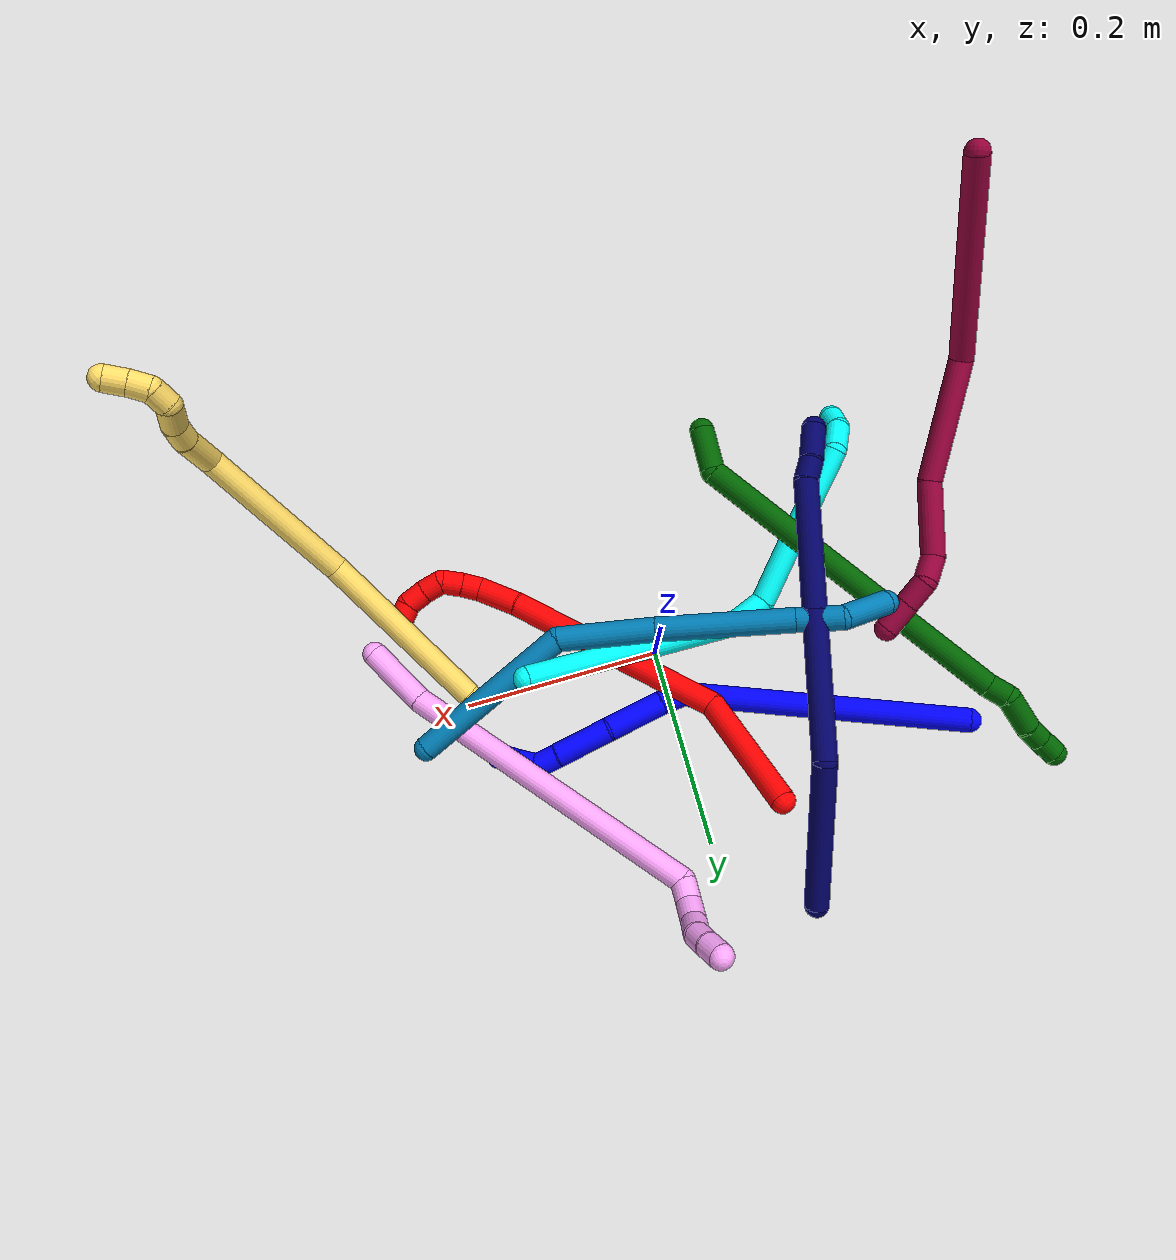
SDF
<sdf version="1.7">
 <world name="default">
  <plugin name="TubeGeneratorPlugin" filename="libtube_generator_plugin.so"/>
  <model name="photoneo_s_sensor">
   <static>1</static>
   <pose>0 0 2 1.57079 1.57079 3.14159</pose>
   <link name="link">
    <inertial><mass>0.1</mass></inertial>
    <sensor name="sensor" type="depth">
     <update_rate>30</update_rate>
     <camera>
      <horizontal_fov>1.22</horizontal_fov>
      <image><width>1920</width><height>1200</height><format>B8G8R8</format></image>
      <clip><near>0.1</near><far>4</far></clip>
      <depth_camera><output>points</output></depth_camera>
     </camera>
     <plugin name="camera_plugin" filename="libgazebo_ros_depth_camera.so">
      <baseline>0.2</baseline>
      <alwaysOn>1</alwaysOn>
      <updateRate>0.0</updateRate>
      <cameraName>camera_ir</cameraName>
      <imageTopicName>/camera/color/image_raw</imageTopicName>
      <cameraInfoTopicName>/camera/color/camera_info</cameraInfoTopicName>
      <depthImageTopicName>/camera/depth/image_raw</depthImageTopicName>
      <depthImageCameraInfoTopicName>/camera/depth/camera_info</depthImageCameraInfoTopicName>
      <pointCloudTopicName>/camera/depth/points</pointCloudTopicName>
      <frameName>fr_optical</frameName>
      <pointCloudCutoff>0.1</pointCloudCutoff>
      <pointCloudCutoffMax>2.0</pointCloudCutoffMax>
      <distortionK1>0</distortionK1>
      <distortionK2>0</distortionK2>
      <distortionK3>0</distortionK3>
      <distortionT1>0</distortionT1>
      <distortionT2>0</distortionT2>
      <CxPrime>0</CxPrime>
      <Cx>0</Cx>
      <Cy>0</Cy>
      <focalLength>0</focalLength>
      <hackBaseline>0</hackBaseline>
     </plugin>
    </sensor>
   </link>
  </model>
  <gravity>0 0 -9.8</gravity>
  <magnetic_field>6e-06 2.3e-05 -4.2e-05</magnetic_field>
  <atmosphere type="adiabatic"/>
  <physics name="default_physics" default="0" type="ode">
   <max_step_size>0.003</max_step_size>
   <real_time_factor>1</real_time_factor>
   <real_time_update_rate>1000</real_time_update_rate>
   <max_contacts>10000</max_contacts>
   <ode>
    <solver>
     <type>quick</type>
     <iters>100</iters>
     <sor>1.3</sor>
     <use_dynamic_moi_rescaling>0</use_dynamic_moi_rescaling>
    </solver>
    <constraints>
     <contact_max_correcting_vel>0</contact_max_correcting_vel>
     <contact_surface_layer>0.001</contact_surface_layer>
     <cfm>0</cfm>
     <erp>0.2</erp>
    </constraints>
   </ode>
  </physics>
  <scene><ambient>0.4 0.4 0.4 1</ambient><background>0.7 0.7 0.7 1</background><shadows>0</shadows></scene>
  <audio><device>default</device></audio>
  <spherical_coordinates>
   <surface_model>EARTH_WGS84</surface_model>
   <latitude_deg>0</latitude_deg>
   <longitude_deg>0</longitude_deg>
   <elevation>0</elevation>
   <heading_deg>0</heading_deg>
  </spherical_coordinates>
  <model name="bin">
   <static>1</static>
   <link name="bottom">
    <collision name="collision-bottom">
     <pose>0 0 -0.01 0 -0 0</pose>
     <geometry><box><size>0.8 0.6 0.02</size></box></geometry>
     <surface>
      <friction><ode><mu>100</mu><mu2>100</mu2></ode></friction>
      <contact><collide_bitmask>65535</collide_bitmask></contact>
     </surface>
    </collision>
   </link>
   <link name="west_wall">
    <collision name="collision-west_wall">
     <pose>-0.41 0 0.1 0 -0 0</pose>
     <geometry><box><size>0.02 0.6 0.2</size></box></geometry>
     <surface>
      <friction><ode><mu>100</mu><mu2>100</mu2></ode></friction>
      <contact><collide_bitmask>65535</collide_bitmask></contact>
     </surface>
    </collision>
   </link>
   <link name="east_wall">
    <collision name="collision-east_wall">
     <pose>0.41 0 0.1 0 -0 0</pose>
     <geometry><box><size>0.02 0.6 0.2</size></box></geometry>
     <surface>
      <friction><ode><mu>100</mu><mu2>100</mu2></ode></friction>
      <contact><collide_bitmask>65535</collide_bitmask></contact>
     </surface>
    </collision>
   </link>
   <link name="south_wall">
    <collision name="collision-south_wall">
     <pose>0 -0.31 0.1 0 -0 0</pose>
     <geometry><box><size>0.8 0.02 0.2</size></box></geometry>
     <surface>
      <friction><ode><mu>100</mu><mu2>100</mu2></ode></friction>
      <contact><collide_bitmask>65535</collide_bitmask></contact>
     </surface>
    </collision>
   </link>
   <link name="north_wall">
    <collision name="collision-north_wall">
     <pose>0 0.31 0.1 0 -0 0</pose>
     <geometry><box><size>0.8 0.02 0.2</size></box></geometry>
     <surface>
      <friction><ode><mu>100</mu><mu2>100</mu2></ode></friction>
      <contact><collide_bitmask>65535</collide_bitmask></contact>
     </surface>
    </collision>
   </link>
  </model>
  <model name="1">
   <static>0</static>
   <link name="1">
    <collision name="collision-cylinder-e_1_1_4">
     <pose>0.132333 -0.04113 0.045461 0.735427 1.13696 0.482608</pose>
     <geometry><cylinder><radius>0.0125</radius><length>0.291688</length></cylinder></geometry>
     <surface>
      <friction><ode><mu>1.16</mu><mu2>1.16</mu2><slip1>0</slip1><slip2>0</slip2></ode></friction>
      <contact><ode><kp>1e+06</kp><kd>1</kd><max_vel>0</max_vel><min_depth>0.001</min_depth></ode></contact>
     </surface>
    </collision>
    <visual name="visual-cylinder-e_1_1_4">
     <pose>0.132333 -0.04113 0.045461 0.735427 1.13696 0.482608</pose>
     <geometry><cylinder><radius>0.0125</radius><length>0.291688</length></cylinder></geometry>
     <material><ambient>0 0 1 1</ambient></material>
    </visual>
    <collision name="collision-cylinder-e_2_4_5">
     <pose>0.276727 -0.079462 0.095332 -0.565523 1.1621 -0.377055</pose>
     <geometry><cylinder><radius>0.0125</radius><length>0.026285</length></cylinder></geometry>
     <surface>
      <friction><ode><mu>1.16</mu><mu2>1.16</mu2><slip1>0</slip1><slip2>0</slip2></ode></friction>
      <contact><ode><kp>1e+06</kp><kd>1</kd><max_vel>0</max_vel><min_depth>0.001</min_depth></ode></contact>
     </surface>
    </collision>
    <visual name="visual-cylinder-e_2_4_5">
     <pose>0.276727 -0.079462 0.095332 -0.565523 1.1621 -0.377055</pose>
     <geometry><cylinder><radius>0.0125</radius><length>0.026285</length></cylinder></geometry>
     <material><ambient>0 0 1 1</ambient></material>
    </visual>
    <collision name="collision-cylinder-e_3_5_6">
     <pose>0.315846 -0.067683 0.109793 -0.729129 1.10867 -0.464004</pose>
     <geometry><cylinder><radius>0.0125</radius><length>0.06046</length></cylinder></geometry>
     <surface>
      <friction><ode><mu>1.16</mu><mu2>1.16</mu2><slip1>0</slip1><slip2>0</slip2></ode></friction>
      <contact><ode><kp>1e+06</kp><kd>1</kd><max_vel>0</max_vel><min_depth>0.001</min_depth></ode></contact>
     </surface>
    </collision>
    <visual name="visual-cylinder-e_3_5_6">
     <pose>0.315846 -0.067683 0.109793 -0.729129 1.10867 -0.464004</pose>
     <geometry><cylinder><radius>0.0125</radius><length>0.06046</length></cylinder></geometry>
     <material><ambient>0 0 1 1</ambient></material>
    </visual>
    <collision name="collision-cylinder-e_4_6_7">
     <pose>0.370415 -0.05164 0.12415 -1.02344 1.27869 -0.791135</pose>
     <geometry><cylinder><radius>0.0125</radius><length>0.057454</length></cylinder></geometry>
     <surface>
      <friction><ode><mu>1.16</mu><mu2>1.16</mu2><slip1>0</slip1><slip2>0</slip2></ode></friction>
      <contact><ode><kp>1e+06</kp><kd>1</kd><max_vel>0</max_vel><min_depth>0.001</min_depth></ode></contact>
     </surface>
    </collision>
    <visual name="visual-cylinder-e_4_6_7">
     <pose>0.370415 -0.05164 0.12415 -1.02344 1.27869 -0.791135</pose>
     <geometry><cylinder><radius>0.0125</radius><length>0.057454</length></cylinder></geometry>
     <material><ambient>0 0 1 1</ambient></material>
    </visual>
    <collision name="collision-cylinder-e_5_7_8">
     <pose>0.40903 -0.041984 0.129482 -1.19343 1.32481 -0.974489</pose>
     <geometry><cylinder><radius>0.0125</radius><length>0.0229</length></cylinder></geometry>
     <surface>
      <friction><ode><mu>1.16</mu><mu2>1.16</mu2><slip1>0</slip1><slip2>0</slip2></ode></friction>
      <contact><ode><kp>1e+06</kp><kd>1</kd><max_vel>0</max_vel><min_depth>0.001</min_depth></ode></contact>
     </surface>
    </collision>
    <visual name="visual-cylinder-e_5_7_8">
     <pose>0.40903 -0.041984 0.129482 -1.19343 1.32481 -0.974489</pose>
     <geometry><cylinder><radius>0.0125</radius><length>0.0229</length></cylinder></geometry>
     <material><ambient>0 0 1 1</ambient></material>
    </visual>
    <collision name="collision-cylinder-e_6_8_9">
     <pose>0.429342 -0.044281 0.131129 1.44479 1.07937 0.971445</pose>
     <geometry><cylinder><radius>0.0125</radius><length>0.020885</length></cylinder></geometry>
     <surface>
      <friction><ode><mu>1.16</mu><mu2>1.16</mu2><slip1>0</slip1><slip2>0</slip2></ode></friction>
      <contact><ode><kp>1e+06</kp><kd>1</kd><max_vel>0</max_vel><min_depth>0.001</min_depth></ode></contact>
     </surface>
    </collision>
    <visual name="visual-cylinder-e_6_8_9">
     <pose>0.429342 -0.044281 0.131129 1.44479 1.07937 0.971445</pose>
     <geometry><cylinder><radius>0.0125</radius><length>0.020885</length></cylinder></geometry>
     <material><ambient>0 0 1 1</ambient></material>
    </visual>
    <collision name="collision-cylinder-e_7_9_2">
     <pose>0.447292 -0.053954 0.133741 1.1761 1.03568 0.72601</pose>
     <geometry><cylinder><radius>0.0125</radius><length>0.020329</length></cylinder></geometry>
     <surface>
      <friction><ode><mu>1.16</mu><mu2>1.16</mu2><slip1>0</slip1><slip2>0</slip2></ode></friction>
      <contact><ode><kp>1e+06</kp><kd>1</kd><max_vel>0</max_vel><min_depth>0.001</min_depth></ode></contact>
     </surface>
    </collision>
    <visual name="visual-cylinder-e_7_9_2">
     <pose>0.447292 -0.053954 0.133741 1.1761 1.03568 0.72601</pose>
     <geometry><cylinder><radius>0.0125</radius><length>0.020329</length></cylinder></geometry>
     <material><ambient>0 0 1 1</ambient></material>
    </visual>
    <collision name="collision-sphere-2">
     <pose>0.456035 -0.058739 0.135734 0 -0 0</pose>
     <geometry><sphere><radius>0.0125</radius></sphere></geometry>
     <surface>
      <friction><ode><mu>1.16</mu><mu2>1.16</mu2><slip1>0</slip1><slip2>0</slip2></ode></friction>
      <contact><ode><kp>1e+06</kp><kd>1</kd><max_vel>0</max_vel><min_depth>0.001</min_depth></ode></contact>
     </surface>
    </collision>
    <visual name="visual-sphere-2">
     <pose>0.456035 -0.058739 0.135734 0 -0 0</pose>
     <geometry><sphere><radius>0.0125</radius></sphere></geometry>
     <material><ambient>0 0 1 1</ambient></material>
    </visual>
    <collision name="collision-sphere-9">
     <pose>0.438548 -0.049169 0.131748 0 -0 0</pose>
     <geometry><sphere><radius>0.0125</radius></sphere></geometry>
     <surface>
      <friction><ode><mu>1.16</mu><mu2>1.16</mu2><slip1>0</slip1><slip2>0</slip2></ode></friction>
      <contact><ode><kp>1e+06</kp><kd>1</kd><max_vel>0</max_vel><min_depth>0.001</min_depth></ode></contact>
     </surface>
    </collision>
    <visual name="visual-sphere-9">
     <pose>0.438548 -0.049169 0.131748 0 -0 0</pose>
     <geometry><sphere><radius>0.0125</radius></sphere></geometry>
     <material><ambient>0 0 1 1</ambient></material>
    </visual>
    <collision name="collision-sphere-4">
     <pose>0.264667 -0.08226 0.090922 0 -0 0</pose>
     <geometry><sphere><radius>0.0125</radius></sphere></geometry>
     <surface>
      <friction><ode><mu>1.16</mu><mu2>1.16</mu2><slip1>0</slip1><slip2>0</slip2></ode></friction>
      <contact><ode><kp>1e+06</kp><kd>1</kd><max_vel>0</max_vel><min_depth>0.001</min_depth></ode></contact>
     </surface>
    </collision>
    <visual name="visual-sphere-4">
     <pose>0.264667 -0.08226 0.090922 0 -0 0</pose>
     <geometry><sphere><radius>0.0125</radius></sphere></geometry>
     <material><ambient>0 0 1 1</ambient></material>
    </visual>
    <collision name="collision-sphere-1">
     <geometry><sphere><radius>0.0125</radius></sphere></geometry>
     <surface>
      <friction><ode><mu>1.16</mu><mu2>1.16</mu2><slip1>0</slip1><slip2>0</slip2></ode></friction>
      <contact><ode><kp>1e+06</kp><kd>1</kd><max_vel>0</max_vel><min_depth>0.001</min_depth></ode></contact>
     </surface>
    </collision>
    <visual name="visual-sphere-1">
     <geometry><sphere><radius>0.0125</radius></sphere></geometry>
     <material><ambient>0 0 1 1</ambient></material>
    </visual>
    <collision name="collision-sphere-8">
     <pose>0.420135 -0.039392 0.13051 0 -0 0</pose>
     <geometry><sphere><radius>0.0125</radius></sphere></geometry>
     <surface>
      <friction><ode><mu>1.16</mu><mu2>1.16</mu2><slip1>0</slip1><slip2>0</slip2></ode></friction>
      <contact><ode><kp>1e+06</kp><kd>1</kd><max_vel>0</max_vel><min_depth>0.001</min_depth></ode></contact>
     </surface>
    </collision>
    <visual name="visual-sphere-8">
     <pose>0.420135 -0.039392 0.13051 0 -0 0</pose>
     <geometry><sphere><radius>0.0125</radius></sphere></geometry>
     <material><ambient>0 0 1 1</ambient></material>
    </visual>
    <collision name="collision-sphere-5">
     <pose>0.288787 -0.076663 0.099741 0 -0 0</pose>
     <geometry><sphere><radius>0.0125</radius></sphere></geometry>
     <surface>
      <friction><ode><mu>1.16</mu><mu2>1.16</mu2><slip1>0</slip1><slip2>0</slip2></ode></friction>
      <contact><ode><kp>1e+06</kp><kd>1</kd><max_vel>0</max_vel><min_depth>0.001</min_depth></ode></contact>
     </surface>
    </collision>
    <visual name="visual-sphere-5">
     <pose>0.288787 -0.076663 0.099741 0 -0 0</pose>
     <geometry><sphere><radius>0.0125</radius></sphere></geometry>
     <material><ambient>0 0 1 1</ambient></material>
    </visual>
    <collision name="collision-sphere-6">
     <pose>0.342905 -0.058704 0.119844 0 -0 0</pose>
     <geometry><sphere><radius>0.0125</radius></sphere></geometry>
     <surface>
      <friction><ode><mu>1.16</mu><mu2>1.16</mu2><slip1>0</slip1><slip2>0</slip2></ode></friction>
      <contact><ode><kp>1e+06</kp><kd>1</kd><max_vel>0</max_vel><min_depth>0.001</min_depth></ode></contact>
     </surface>
    </collision>
    <visual name="visual-sphere-6">
     <pose>0.342905 -0.058704 0.119844 0 -0 0</pose>
     <geometry><sphere><radius>0.0125</radius></sphere></geometry>
     <material><ambient>0 0 1 1</ambient></material>
    </visual>
    <collision name="collision-sphere-7">
     <pose>0.397925 -0.044576 0.128455 0 -0 0</pose>
     <geometry><sphere><radius>0.0125</radius></sphere></geometry>
     <surface>
      <friction><ode><mu>1.16</mu><mu2>1.16</mu2><slip1>0</slip1><slip2>0</slip2></ode></friction>
      <contact><ode><kp>1e+06</kp><kd>1</kd><max_vel>0</max_vel><min_depth>0.001</min_depth></ode></contact>
     </surface>
    </collision>
    <visual name="visual-sphere-7">
     <pose>0.397925 -0.044576 0.128455 0 -0 0</pose>
     <geometry><sphere><radius>0.0125</radius></sphere></geometry>
     <material><ambient>0 0 1 1</ambient></material>
    </visual>
    <inertial>
     <pose>0.227356 -0.048256 0.075919 0 -0 0</pose>
     <mass>0.5</mass>
     <inertia>
      <ixx>0.001222</ixx>
      <ixy>0</ixy>
      <ixz>0</ixz>
      <iyy>0.00239</iyy>
      <iyz>0</iyz>
      <izz>-0.001343</izz>
     </inertia>
    </inertial>
   </link>
   <pose>-0.287516 0.154759 0.012457 0.255414 0.252138 -0.012266</pose>
  </model>
  <model name="2">
   <static>0</static>
   <link name="2">
    <collision name="collision-cylinder-e_1_1_4">
     <pose>-0.00595 0.000196 -0.063327 -3.13849 -0.093684 3.07544</pose>
     <geometry><cylinder><radius>0.0125</radius><length>0.127213</length></cylinder></geometry>
     <surface>
      <friction><ode><mu>1.16</mu><mu2>1.16</mu2><slip1>0</slip1><slip2>0</slip2></ode></friction>
      <contact><ode><kp>1e+06</kp><kd>1</kd><max_vel>0</max_vel><min_depth>0.001</min_depth></ode></contact>
     </surface>
    </collision>
    <visual name="visual-cylinder-e_1_1_4">
     <pose>-0.00595 0.000196 -0.063327 -3.13849 -0.093684 3.07544</pose>
     <geometry><cylinder><radius>0.0125</radius><length>0.127213</length></cylinder></geometry>
     <material><ambient>1 0 0 1</ambient></material>
    </visual>
    <collision name="collision-cylinder-e_2_4_5">
     <pose>0.025807 -0.048169 -0.221042 2.66642 0.341334 1.23706</pose>
     <geometry><cylinder><radius>0.0125</radius><length>0.225292</length></cylinder></geometry>
     <surface>
      <friction><ode><mu>1.16</mu><mu2>1.16</mu2><slip1>0</slip1><slip2>0</slip2></ode></friction>
      <contact><ode><kp>1e+06</kp><kd>1</kd><max_vel>0</max_vel><min_depth>0.001</min_depth></ode></contact>
     </surface>
    </collision>
    <visual name="visual-cylinder-e_2_4_5">
     <pose>0.025807 -0.048169 -0.221042 2.66642 0.341334 1.23706</pose>
     <geometry><cylinder><radius>0.0125</radius><length>0.225292</length></cylinder></geometry>
     <material><ambient>1 0 0 1</ambient></material>
    </visual>
    <collision name="collision-cylinder-e_3_5_6">
     <pose>0.072527 -0.103909 -0.333699 2.76717 0.430408 1.71348</pose>
     <geometry><cylinder><radius>0.0125</radius><length>0.043199</length></cylinder></geometry>
     <surface>
      <friction><ode><mu>1.16</mu><mu2>1.16</mu2><slip1>0</slip1><slip2>0</slip2></ode></friction>
      <contact><ode><kp>1e+06</kp><kd>1</kd><max_vel>0</max_vel><min_depth>0.001</min_depth></ode></contact>
     </surface>
    </collision>
    <visual name="visual-cylinder-e_3_5_6">
     <pose>0.072527 -0.103909 -0.333699 2.76717 0.430408 1.71348</pose>
     <geometry><cylinder><radius>0.0125</radius><length>0.043199</length></cylinder></geometry>
     <material><ambient>1 0 0 1</ambient></material>
    </visual>
    <collision name="collision-cylinder-e_4_6_7">
     <pose>0.086894 -0.117677 -0.357784 2.29394 0.547225 1.11296</pose>
     <geometry><cylinder><radius>0.0125</radius><length>0.020582</length></cylinder></geometry>
     <surface>
      <friction><ode><mu>1.16</mu><mu2>1.16</mu2><slip1>0</slip1><slip2>0</slip2></ode></friction>
      <contact><ode><kp>1e+06</kp><kd>1</kd><max_vel>0</max_vel><min_depth>0.001</min_depth></ode></contact>
     </surface>
    </collision>
    <visual name="visual-cylinder-e_4_6_7">
     <pose>0.086894 -0.117677 -0.357784 2.29394 0.547225 1.11296</pose>
     <geometry><cylinder><radius>0.0125</radius><length>0.020582</length></cylinder></geometry>
     <material><ambient>1 0 0 1</ambient></material>
    </visual>
    <collision name="collision-cylinder-e_5_7_8">
     <pose>0.098331 -0.130899 -0.368565 2.2134 0.633188 1.15905</pose>
     <geometry><cylinder><radius>0.0125</radius><length>0.020558</length></cylinder></geometry>
     <surface>
      <friction><ode><mu>1.16</mu><mu2>1.16</mu2><slip1>0</slip1><slip2>0</slip2></ode></friction>
      <contact><ode><kp>1e+06</kp><kd>1</kd><max_vel>0</max_vel><min_depth>0.001</min_depth></ode></contact>
     </surface>
    </collision>
    <visual name="visual-cylinder-e_5_7_8">
     <pose>0.098331 -0.130899 -0.368565 2.2134 0.633188 1.15905</pose>
     <geometry><cylinder><radius>0.0125</radius><length>0.020558</length></cylinder></geometry>
     <material><ambient>1 0 0 1</ambient></material>
    </visual>
    <collision name="collision-cylinder-e_6_8_9">
     <pose>0.114282 -0.138137 -0.376029 2.90436 1.31599 2.83562</pose>
     <geometry><cylinder><radius>0.0125</radius><length>0.020396</length></cylinder></geometry>
     <surface>
      <friction><ode><mu>1.16</mu><mu2>1.16</mu2><slip1>0</slip1><slip2>0</slip2></ode></friction>
      <contact><ode><kp>1e+06</kp><kd>1</kd><max_vel>0</max_vel><min_depth>0.001</min_depth></ode></contact>
     </surface>
    </collision>
    <visual name="visual-cylinder-e_6_8_9">
     <pose>0.114282 -0.138137 -0.376029 2.90436 1.31599 2.83562</pose>
     <geometry><cylinder><radius>0.0125</radius><length>0.020396</length></cylinder></geometry>
     <material><ambient>1 0 0 1</ambient></material>
    </visual>
    <collision name="collision-cylinder-e_7_9_10">
     <pose>0.134819 -0.13979 -0.37915 2.10654 1.45699 2.00573</pose>
     <geometry><cylinder><radius>0.0125</radius><length>0.021475</length></cylinder></geometry>
     <surface>
      <friction><ode><mu>1.16</mu><mu2>1.16</mu2><slip1>0</slip1><slip2>0</slip2></ode></friction>
      <contact><ode><kp>1e+06</kp><kd>1</kd><max_vel>0</max_vel><min_depth>0.001</min_depth></ode></contact>
     </surface>
    </collision>
    <visual name="visual-cylinder-e_7_9_10">
     <pose>0.134819 -0.13979 -0.37915 2.10654 1.45699 2.00573</pose>
     <geometry><cylinder><radius>0.0125</radius><length>0.021475</length></cylinder></geometry>
     <material><ambient>1 0 0 1</ambient></material>
    </visual>
    <collision name="collision-cylinder-e_8_10_2">
     <pose>0.155258 -0.138746 -0.37611 -0.518925 1.16331 -0.345598</pose>
     <geometry><cylinder><radius>0.0125</radius><length>0.021286</length></cylinder></geometry>
     <surface>
      <friction><ode><mu>1.16</mu><mu2>1.16</mu2><slip1>0</slip1><slip2>0</slip2></ode></friction>
      <contact><ode><kp>1e+06</kp><kd>1</kd><max_vel>0</max_vel><min_depth>0.001</min_depth></ode></contact>
     </surface>
    </collision>
    <visual name="visual-cylinder-e_8_10_2">
     <pose>0.155258 -0.138746 -0.37611 -0.518925 1.16331 -0.345598</pose>
     <geometry><cylinder><radius>0.0125</radius><length>0.021286</length></cylinder></geometry>
     <material><ambient>1 0 0 1</ambient></material>
    </visual>
    <collision name="collision-sphere-2">
     <pose>0.16503 -0.136655 -0.372448 0 -0 0</pose>
     <geometry><sphere><radius>0.0125</radius></sphere></geometry>
     <surface>
      <friction><ode><mu>1.16</mu><mu2>1.16</mu2><slip1>0</slip1><slip2>0</slip2></ode></friction>
      <contact><ode><kp>1e+06</kp><kd>1</kd><max_vel>0</max_vel><min_depth>0.001</min_depth></ode></contact>
     </surface>
    </collision>
    <visual name="visual-sphere-2">
     <pose>0.16503 -0.136655 -0.372448 0 -0 0</pose>
     <geometry><sphere><radius>0.0125</radius></sphere></geometry>
     <material><ambient>1 0 0 1</ambient></material>
    </visual>
    <collision name="collision-sphere-10">
     <pose>0.145487 -0.140838 -0.379773 0 -0 0</pose>
     <geometry><sphere><radius>0.0125</radius></sphere></geometry>
     <surface>
      <friction><ode><mu>1.16</mu><mu2>1.16</mu2><slip1>0</slip1><slip2>0</slip2></ode></friction>
      <contact><ode><kp>1e+06</kp><kd>1</kd><max_vel>0</max_vel><min_depth>0.001</min_depth></ode></contact>
     </surface>
    </collision>
    <visual name="visual-sphere-10">
     <pose>0.145487 -0.140838 -0.379773 0 -0 0</pose>
     <geometry><sphere><radius>0.0125</radius></sphere></geometry>
     <material><ambient>1 0 0 1</ambient></material>
    </visual>
    <collision name="collision-sphere-9">
     <pose>0.12415 -0.138741 -0.378528 0 -0 0</pose>
     <geometry><sphere><radius>0.0125</radius></sphere></geometry>
     <surface>
      <friction><ode><mu>1.16</mu><mu2>1.16</mu2><slip1>0</slip1><slip2>0</slip2></ode></friction>
      <contact><ode><kp>1e+06</kp><kd>1</kd><max_vel>0</max_vel><min_depth>0.001</min_depth></ode></contact>
     </surface>
    </collision>
    <visual name="visual-sphere-9">
     <pose>0.12415 -0.138741 -0.378528 0 -0 0</pose>
     <geometry><sphere><radius>0.0125</radius></sphere></geometry>
     <material><ambient>1 0 0 1</ambient></material>
    </visual>
    <collision name="collision-sphere-4">
     <pose>-0.0119 0.000393 -0.126654 0 -0 0</pose>
     <geometry><sphere><radius>0.0125</radius></sphere></geometry>
     <surface>
      <friction><ode><mu>1.16</mu><mu2>1.16</mu2><slip1>0</slip1><slip2>0</slip2></ode></friction>
      <contact><ode><kp>1e+06</kp><kd>1</kd><max_vel>0</max_vel><min_depth>0.001</min_depth></ode></contact>
     </surface>
    </collision>
    <visual name="visual-sphere-4">
     <pose>-0.0119 0.000393 -0.126654 0 -0 0</pose>
     <geometry><sphere><radius>0.0125</radius></sphere></geometry>
     <material><ambient>1 0 0 1</ambient></material>
    </visual>
    <collision name="collision-sphere-1">
     <geometry><sphere><radius>0.0125</radius></sphere></geometry>
     <surface>
      <friction><ode><mu>1.16</mu><mu2>1.16</mu2><slip1>0</slip1><slip2>0</slip2></ode></friction>
      <contact><ode><kp>1e+06</kp><kd>1</kd><max_vel>0</max_vel><min_depth>0.001</min_depth></ode></contact>
     </surface>
    </collision>
    <visual name="visual-sphere-1">
     <geometry><sphere><radius>0.0125</radius></sphere></geometry>
     <material><ambient>1 0 0 1</ambient></material>
    </visual>
    <collision name="collision-sphere-8">
     <pose>0.104413 -0.137533 -0.373531 0 -0 0</pose>
     <geometry><sphere><radius>0.0125</radius></sphere></geometry>
     <surface>
      <friction><ode><mu>1.16</mu><mu2>1.16</mu2><slip1>0</slip1><slip2>0</slip2></ode></friction>
      <contact><ode><kp>1e+06</kp><kd>1</kd><max_vel>0</max_vel><min_depth>0.001</min_depth></ode></contact>
     </surface>
    </collision>
    <visual name="visual-sphere-8">
     <pose>0.104413 -0.137533 -0.373531 0 -0 0</pose>
     <geometry><sphere><radius>0.0125</radius></sphere></geometry>
     <material><ambient>1 0 0 1</ambient></material>
    </visual>
    <collision name="collision-sphere-5">
     <pose>0.063515 -0.09673 -0.315429 0 -0 0</pose>
     <geometry><sphere><radius>0.0125</radius></sphere></geometry>
     <surface>
      <friction><ode><mu>1.16</mu><mu2>1.16</mu2><slip1>0</slip1><slip2>0</slip2></ode></friction>
      <contact><ode><kp>1e+06</kp><kd>1</kd><max_vel>0</max_vel><min_depth>0.001</min_depth></ode></contact>
     </surface>
    </collision>
    <visual name="visual-sphere-5">
     <pose>0.063515 -0.09673 -0.315429 0 -0 0</pose>
     <geometry><sphere><radius>0.0125</radius></sphere></geometry>
     <material><ambient>1 0 0 1</ambient></material>
    </visual>
    <collision name="collision-sphere-6">
     <pose>0.081539 -0.111089 -0.351968 0 -0 0</pose>
     <geometry><sphere><radius>0.0125</radius></sphere></geometry>
     <surface>
      <friction><ode><mu>1.16</mu><mu2>1.16</mu2><slip1>0</slip1><slip2>0</slip2></ode></friction>
      <contact><ode><kp>1e+06</kp><kd>1</kd><max_vel>0</max_vel><min_depth>0.001</min_depth></ode></contact>
     </surface>
    </collision>
    <visual name="visual-sphere-6">
     <pose>0.081539 -0.111089 -0.351968 0 -0 0</pose>
     <geometry><sphere><radius>0.0125</radius></sphere></geometry>
     <material><ambient>1 0 0 1</ambient></material>
    </visual>
    <collision name="collision-sphere-7">
     <pose>0.092248 -0.124266 -0.363599 0 -0 0</pose>
     <geometry><sphere><radius>0.0125</radius></sphere></geometry>
     <surface>
      <friction><ode><mu>1.16</mu><mu2>1.16</mu2><slip1>0</slip1><slip2>0</slip2></ode></friction>
      <contact><ode><kp>1e+06</kp><kd>1</kd><max_vel>0</max_vel><min_depth>0.001</min_depth></ode></contact>
     </surface>
    </collision>
    <visual name="visual-sphere-7">
     <pose>0.092248 -0.124266 -0.363599 0 -0 0</pose>
     <geometry><sphere><radius>0.0125</radius></sphere></geometry>
     <material><ambient>1 0 0 1</ambient></material>
    </visual>
    <inertial>
     <pose>0.041062 -0.058403 -0.222057 0 -0 0</pose>
     <mass>0.5</mass>
     <inertia><ixx>0.001012</ixx><ixy>0</ixy><ixz>0</ixz><iyy>0.00091</iyy><iyz>0</iyz><izz>7.4e-05</izz></inertia>
    </inertial>
   </link>
   <pose>-0.069962 0.176857 0.098161 -1.06136 0.148963 0.472061</pose>
  </model>
  <model name="3">
   <static>0</static>
   <link name="3">
    <collision name="collision-cylinder-e_1_1_4">
     <pose>-0.044591 0.014558 0.105591 -0.137004 -0.396214 0.027544</pose>
     <geometry><cylinder><radius>0.0125</radius><length>0.231082</length></cylinder></geometry>
     <surface>
      <friction><ode><mu>1.16</mu><mu2>1.16</mu2><slip1>0</slip1><slip2>0</slip2></ode></friction>
      <contact><ode><kp>1e+06</kp><kd>1</kd><max_vel>0</max_vel><min_depth>0.001</min_depth></ode></contact>
     </surface>
    </collision>
    <visual name="visual-cylinder-e_1_1_4">
     <pose>-0.044591 0.014558 0.105591 -0.137004 -0.396214 0.027544</pose>
     <geometry><cylinder><radius>0.0125</radius><length>0.231082</length></cylinder></geometry>
     <material><ambient>0.003922 1 0.996078 1</ambient></material>
    </visual>
    <collision name="collision-cylinder-e_2_4_5">
     <pose>-0.088612 0.029142 0.230666 -0.001383 0.029188 -2e-05</pose>
     <geometry><cylinder><radius>0.0125</radius><length>0.038985</length></cylinder></geometry>
     <surface>
      <friction><ode><mu>1.16</mu><mu2>1.16</mu2><slip1>0</slip1><slip2>0</slip2></ode></friction>
      <contact><ode><kp>1e+06</kp><kd>1</kd><max_vel>0</max_vel><min_depth>0.001</min_depth></ode></contact>
     </surface>
    </collision>
    <visual name="visual-cylinder-e_2_4_5">
     <pose>-0.088612 0.029142 0.230666 -0.001383 0.029188 -2e-05</pose>
     <geometry><cylinder><radius>0.0125</radius><length>0.038985</length></cylinder></geometry>
     <material><ambient>0.003922 1 0.996078 1</ambient></material>
    </visual>
    <collision name="collision-cylinder-e_3_5_6">
     <pose>-0.067881 0.019706 0.285033 0.264912 0.508844 0.069271</pose>
     <geometry><cylinder><radius>0.0125</radius><length>0.082772</length></cylinder></geometry>
     <surface>
      <friction><ode><mu>1.16</mu><mu2>1.16</mu2><slip1>0</slip1><slip2>0</slip2></ode></friction>
      <contact><ode><kp>1e+06</kp><kd>1</kd><max_vel>0</max_vel><min_depth>0.001</min_depth></ode></contact>
     </surface>
    </collision>
    <visual name="visual-cylinder-e_3_5_6">
     <pose>-0.067881 0.019706 0.285033 0.264912 0.508844 0.069271</pose>
     <geometry><cylinder><radius>0.0125</radius><length>0.082772</length></cylinder></geometry>
     <material><ambient>0.003922 1 0.996078 1</ambient></material>
    </visual>
    <collision name="collision-cylinder-e_4_6_7">
     <pose>-0.02818 -0.001098 0.359246 0.280726 0.445351 0.063964</pose>
     <geometry><cylinder><radius>0.0125</radius><length>0.090715</length></cylinder></geometry>
     <surface>
      <friction><ode><mu>1.16</mu><mu2>1.16</mu2><slip1>0</slip1><slip2>0</slip2></ode></friction>
      <contact><ode><kp>1e+06</kp><kd>1</kd><max_vel>0</max_vel><min_depth>0.001</min_depth></ode></contact>
     </surface>
    </collision>
    <visual name="visual-cylinder-e_4_6_7">
     <pose>-0.02818 -0.001098 0.359246 0.280726 0.445351 0.063964</pose>
     <geometry><cylinder><radius>0.0125</radius><length>0.090715</length></cylinder></geometry>
     <material><ambient>0.003922 1 0.996078 1</ambient></material>
    </visual>
    <collision name="collision-cylinder-e_5_7_8">
     <pose>-0.008545 -0.024029 0.410607 0.766798 0.005761 0.002324</pose>
     <geometry><cylinder><radius>0.0125</radius><length>0.033411</length></cylinder></geometry>
     <surface>
      <friction><ode><mu>1.16</mu><mu2>1.16</mu2><slip1>0</slip1><slip2>0</slip2></ode></friction>
      <contact><ode><kp>1e+06</kp><kd>1</kd><max_vel>0</max_vel><min_depth>0.001</min_depth></ode></contact>
     </surface>
    </collision>
    <visual name="visual-cylinder-e_5_7_8">
     <pose>-0.008545 -0.024029 0.410607 0.766798 0.005761 0.002324</pose>
     <geometry><cylinder><radius>0.0125</radius><length>0.033411</length></cylinder></geometry>
     <material><ambient>0.003922 1 0.996078 1</ambient></material>
    </visual>
    <collision name="collision-cylinder-e_6_8_2">
     <pose>-0.010393 -0.046218 0.426705 1.2043 -0.169561 -0.116686</pose>
     <geometry><cylinder><radius>0.0125</radius><length>0.023035</length></cylinder></geometry>
     <surface>
      <friction><ode><mu>1.16</mu><mu2>1.16</mu2><slip1>0</slip1><slip2>0</slip2></ode></friction>
      <contact><ode><kp>1e+06</kp><kd>1</kd><max_vel>0</max_vel><min_depth>0.001</min_depth></ode></contact>
     </surface>
    </collision>
    <visual name="visual-cylinder-e_6_8_2">
     <pose>-0.010393 -0.046218 0.426705 1.2043 -0.169561 -0.116686</pose>
     <geometry><cylinder><radius>0.0125</radius><length>0.023035</length></cylinder></geometry>
     <material><ambient>0.003922 1 0.996078 1</ambient></material>
    </visual>
    <collision name="collision-sphere-2">
     <pose>-0.012336 -0.056816 0.430773 0 -0 0</pose>
     <geometry><sphere><radius>0.0125</radius></sphere></geometry>
     <surface>
      <friction><ode><mu>1.16</mu><mu2>1.16</mu2><slip1>0</slip1><slip2>0</slip2></ode></friction>
      <contact><ode><kp>1e+06</kp><kd>1</kd><max_vel>0</max_vel><min_depth>0.001</min_depth></ode></contact>
     </surface>
    </collision>
    <visual name="visual-sphere-2">
     <pose>-0.012336 -0.056816 0.430773 0 -0 0</pose>
     <geometry><sphere><radius>0.0125</radius></sphere></geometry>
     <material><ambient>0.003922 1 0.996078 1</ambient></material>
    </visual>
    <collision name="collision-sphere-4">
     <pose>-0.089181 0.029115 0.211182 0 -0 0</pose>
     <geometry><sphere><radius>0.0125</radius></sphere></geometry>
     <surface>
      <friction><ode><mu>1.16</mu><mu2>1.16</mu2><slip1>0</slip1><slip2>0</slip2></ode></friction>
      <contact><ode><kp>1e+06</kp><kd>1</kd><max_vel>0</max_vel><min_depth>0.001</min_depth></ode></contact>
     </surface>
    </collision>
    <visual name="visual-sphere-4">
     <pose>-0.089181 0.029115 0.211182 0 -0 0</pose>
     <geometry><sphere><radius>0.0125</radius></sphere></geometry>
     <material><ambient>0.003922 1 0.996078 1</ambient></material>
    </visual>
    <collision name="collision-sphere-1">
     <geometry><sphere><radius>0.0125</radius></sphere></geometry>
     <surface>
      <friction><ode><mu>1.16</mu><mu2>1.16</mu2><slip1>0</slip1><slip2>0</slip2></ode></friction>
      <contact><ode><kp>1e+06</kp><kd>1</kd><max_vel>0</max_vel><min_depth>0.001</min_depth></ode></contact>
     </surface>
    </collision>
    <visual name="visual-sphere-1">
     <geometry><sphere><radius>0.0125</radius></sphere></geometry>
     <material><ambient>0.003922 1 0.996078 1</ambient></material>
    </visual>
    <collision name="collision-sphere-8">
     <pose>-0.008449 -0.03562 0.422637 0 -0 0</pose>
     <geometry><sphere><radius>0.0125</radius></sphere></geometry>
     <surface>
      <friction><ode><mu>1.16</mu><mu2>1.16</mu2><slip1>0</slip1><slip2>0</slip2></ode></friction>
      <contact><ode><kp>1e+06</kp><kd>1</kd><max_vel>0</max_vel><min_depth>0.001</min_depth></ode></contact>
     </surface>
    </collision>
    <visual name="visual-sphere-8">
     <pose>-0.008449 -0.03562 0.422637 0 -0 0</pose>
     <geometry><sphere><radius>0.0125</radius></sphere></geometry>
     <material><ambient>0.003922 1 0.996078 1</ambient></material>
    </visual>
    <collision name="collision-sphere-5">
     <pose>-0.088043 0.029169 0.250151 0 -0 0</pose>
     <geometry><sphere><radius>0.0125</radius></sphere></geometry>
     <surface>
      <friction><ode><mu>1.16</mu><mu2>1.16</mu2><slip1>0</slip1><slip2>0</slip2></ode></friction>
      <contact><ode><kp>1e+06</kp><kd>1</kd><max_vel>0</max_vel><min_depth>0.001</min_depth></ode></contact>
     </surface>
    </collision>
    <visual name="visual-sphere-5">
     <pose>-0.088043 0.029169 0.250151 0 -0 0</pose>
     <geometry><sphere><radius>0.0125</radius></sphere></geometry>
     <material><ambient>0.003922 1 0.996078 1</ambient></material>
    </visual>
    <collision name="collision-sphere-6">
     <pose>-0.047719 0.010243 0.319915 0 -0 0</pose>
     <geometry><sphere><radius>0.0125</radius></sphere></geometry>
     <surface>
      <friction><ode><mu>1.16</mu><mu2>1.16</mu2><slip1>0</slip1><slip2>0</slip2></ode></friction>
      <contact><ode><kp>1e+06</kp><kd>1</kd><max_vel>0</max_vel><min_depth>0.001</min_depth></ode></contact>
     </surface>
    </collision>
    <visual name="visual-sphere-6">
     <pose>-0.047719 0.010243 0.319915 0 -0 0</pose>
     <geometry><sphere><radius>0.0125</radius></sphere></geometry>
     <material><ambient>0.003922 1 0.996078 1</ambient></material>
    </visual>
    <collision name="collision-sphere-7">
     <pose>-0.008641 -0.012439 0.398577 0 -0 0</pose>
     <geometry><sphere><radius>0.0125</radius></sphere></geometry>
     <surface>
      <friction><ode><mu>1.16</mu><mu2>1.16</mu2><slip1>0</slip1><slip2>0</slip2></ode></friction>
      <contact><ode><kp>1e+06</kp><kd>1</kd><max_vel>0</max_vel><min_depth>0.001</min_depth></ode></contact>
     </surface>
    </collision>
    <visual name="visual-sphere-7">
     <pose>-0.008641 -0.012439 0.398577 0 -0 0</pose>
     <geometry><sphere><radius>0.0125</radius></sphere></geometry>
     <material><ambient>0.003922 1 0.996078 1</ambient></material>
    </visual>
    <inertial>
     <pose>-0.044917 0.008328 0.226245 0 -0 0</pose>
     <mass>0.5</mass>
     <inertia>
      <ixx>0.001105</ixx>
      <ixy>0</ixy>
      <ixz>0</ixz>
      <iyy>0.00118</iyy>
      <iyz>0</iyz>
      <izz>0.000283</izz>
     </inertia>
    </inertial>
   </link>
   <pose>0.13222 -0.001566 0.09119 1.72762 -0.982747 -1.33915</pose>
  </model>
  <model name="4">
   <static>0</static>
   <link name="4">
    <collision name="collision-cylinder-e_1_1_4">
     <pose>-0.006771 0.026937 0.01987 -0.935239 -0.199601 0.101044</pose>
     <geometry><cylinder><radius>0.0125</radius><length>0.068302</length></cylinder></geometry>
     <surface>
      <friction><ode><mu>1.16</mu><mu2>1.16</mu2><slip1>0</slip1><slip2>0</slip2></ode></friction>
      <contact><ode><kp>1e+06</kp><kd>1</kd><max_vel>0</max_vel><min_depth>0.001</min_depth></ode></contact>
     </surface>
    </collision>
    <visual name="visual-cylinder-e_1_1_4">
     <pose>-0.006771 0.026937 0.01987 -0.935239 -0.199601 0.101044</pose>
     <geometry><cylinder><radius>0.0125</radius><length>0.068302</length></cylinder></geometry>
     <material><ambient>1 0.65098 0.996078 1</ambient></material>
    </visual>
    <collision name="collision-cylinder-e_2_4_5">
     <pose>-0.07713 0.169695 0.130606 -0.905561 -0.407739 0.200481</pose>
     <geometry><cylinder><radius>0.0125</radius><length>0.320713</length></cylinder></geometry>
     <surface>
      <friction><ode><mu>1.16</mu><mu2>1.16</mu2><slip1>0</slip1><slip2>0</slip2></ode></friction>
      <contact><ode><kp>1e+06</kp><kd>1</kd><max_vel>0</max_vel><min_depth>0.001</min_depth></ode></contact>
     </surface>
    </collision>
    <visual name="visual-cylinder-e_2_4_5">
     <pose>-0.07713 0.169695 0.130606 -0.905561 -0.407739 0.200481</pose>
     <geometry><cylinder><radius>0.0125</radius><length>0.320713</length></cylinder></geometry>
     <material><ambient>1 0.65098 0.996078 1</ambient></material>
    </visual>
    <collision name="collision-cylinder-e_3_5_6">
     <pose>-0.13846 0.290705 0.230623 -0.515746 0.21133 -0.055931</pose>
     <geometry><cylinder><radius>0.0125</radius><length>0.021521</length></cylinder></geometry>
     <surface>
      <friction><ode><mu>1.16</mu><mu2>1.16</mu2><slip1>0</slip1><slip2>0</slip2></ode></friction>
      <contact><ode><kp>1e+06</kp><kd>1</kd><max_vel>0</max_vel><min_depth>0.001</min_depth></ode></contact>
     </surface>
    </collision>
    <visual name="visual-cylinder-e_3_5_6">
     <pose>-0.13846 0.290705 0.230623 -0.515746 0.21133 -0.055931</pose>
     <geometry><cylinder><radius>0.0125</radius><length>0.021521</length></cylinder></geometry>
     <material><ambient>1 0.65098 0.996078 1</ambient></material>
    </visual>
    <collision name="collision-cylinder-e_4_6_7">
     <pose>-0.136389 0.296351 0.252372 -0.036328 -0.014819 0.000269</pose>
     <geometry><cylinder><radius>0.0125</radius><length>0.025213</length></cylinder></geometry>
     <surface>
      <friction><ode><mu>1.16</mu><mu2>1.16</mu2><slip1>0</slip1><slip2>0</slip2></ode></friction>
      <contact><ode><kp>1e+06</kp><kd>1</kd><max_vel>0</max_vel><min_depth>0.001</min_depth></ode></contact>
     </surface>
    </collision>
    <visual name="visual-cylinder-e_4_6_7">
     <pose>-0.136389 0.296351 0.252372 -0.036328 -0.014819 0.000269</pose>
     <geometry><cylinder><radius>0.0125</radius><length>0.025213</length></cylinder></geometry>
     <material><ambient>1 0.65098 0.996078 1</ambient></material>
    </visual>
    <collision name="collision-cylinder-e_5_7_8">
     <pose>-0.138411 0.293536 0.276181 0.284028 -0.15582 -0.022323</pose>
     <geometry><cylinder><radius>0.0125</radius><length>0.023646</length></cylinder></geometry>
     <surface>
      <friction><ode><mu>1.16</mu><mu2>1.16</mu2><slip1>0</slip1><slip2>0</slip2></ode></friction>
      <contact><ode><kp>1e+06</kp><kd>1</kd><max_vel>0</max_vel><min_depth>0.001</min_depth></ode></contact>
     </surface>
    </collision>
    <visual name="visual-cylinder-e_5_7_8">
     <pose>-0.138411 0.293536 0.276181 0.284028 -0.15582 -0.022323</pose>
     <geometry><cylinder><radius>0.0125</radius><length>0.023646</length></cylinder></geometry>
     <material><ambient>1 0.65098 0.996078 1</ambient></material>
    </visual>
    <collision name="collision-cylinder-e_6_8_9">
     <pose>-0.144555 0.290224 0.296585 0.004293 -0.438412 -0.000956</pose>
     <geometry><cylinder><radius>0.0125</radius><length>0.020304</length></cylinder></geometry>
     <surface>
      <friction><ode><mu>1.16</mu><mu2>1.16</mu2><slip1>0</slip1><slip2>0</slip2></ode></friction>
      <contact><ode><kp>1e+06</kp><kd>1</kd><max_vel>0</max_vel><min_depth>0.001</min_depth></ode></contact>
     </surface>
    </collision>
    <visual name="visual-cylinder-e_6_8_9">
     <pose>-0.144555 0.290224 0.296585 0.004293 -0.438412 -0.000956</pose>
     <geometry><cylinder><radius>0.0125</radius><length>0.020304</length></cylinder></geometry>
     <material><ambient>1 0.65098 0.996078 1</ambient></material>
    </visual>
    <collision name="collision-cylinder-e_7_9_2">
     <pose>-0.153262 0.291539 0.314824 -0.148568 -0.448026 0.033908</pose>
     <geometry><cylinder><radius>0.0125</radius><length>0.020301</length></cylinder></geometry>
     <surface>
      <friction><ode><mu>1.16</mu><mu2>1.16</mu2><slip1>0</slip1><slip2>0</slip2></ode></friction>
      <contact><ode><kp>1e+06</kp><kd>1</kd><max_vel>0</max_vel><min_depth>0.001</min_depth></ode></contact>
     </surface>
    </collision>
    <visual name="visual-cylinder-e_7_9_2">
     <pose>-0.153262 0.291539 0.314824 -0.148568 -0.448026 0.033908</pose>
     <geometry><cylinder><radius>0.0125</radius><length>0.020301</length></cylinder></geometry>
     <material><ambient>1 0.65098 0.996078 1</ambient></material>
    </visual>
    <collision name="collision-sphere-2">
     <pose>-0.157659 0.292893 0.323872 0 -0 0</pose>
     <geometry><sphere><radius>0.0125</radius></sphere></geometry>
     <surface>
      <friction><ode><mu>1.16</mu><mu2>1.16</mu2><slip1>0</slip1><slip2>0</slip2></ode></friction>
      <contact><ode><kp>1e+06</kp><kd>1</kd><max_vel>0</max_vel><min_depth>0.001</min_depth></ode></contact>
     </surface>
    </collision>
    <visual name="visual-sphere-2">
     <pose>-0.157659 0.292893 0.323872 0 -0 0</pose>
     <geometry><sphere><radius>0.0125</radius></sphere></geometry>
     <material><ambient>1 0.65098 0.996078 1</ambient></material>
    </visual>
    <collision name="collision-sphere-9">
     <pose>-0.148865 0.290184 0.305776 0 -0 0</pose>
     <geometry><sphere><radius>0.0125</radius></sphere></geometry>
     <surface>
      <friction><ode><mu>1.16</mu><mu2>1.16</mu2><slip1>0</slip1><slip2>0</slip2></ode></friction>
      <contact><ode><kp>1e+06</kp><kd>1</kd><max_vel>0</max_vel><min_depth>0.001</min_depth></ode></contact>
     </surface>
    </collision>
    <visual name="visual-sphere-9">
     <pose>-0.148865 0.290184 0.305776 0 -0 0</pose>
     <geometry><sphere><radius>0.0125</radius></sphere></geometry>
     <material><ambient>1 0.65098 0.996078 1</ambient></material>
    </visual>
    <collision name="collision-sphere-4">
     <pose>-0.013543 0.053874 0.039741 0 -0 0</pose>
     <geometry><sphere><radius>0.0125</radius></sphere></geometry>
     <surface>
      <friction><ode><mu>1.16</mu><mu2>1.16</mu2><slip1>0</slip1><slip2>0</slip2></ode></friction>
      <contact><ode><kp>1e+06</kp><kd>1</kd><max_vel>0</max_vel><min_depth>0.001</min_depth></ode></contact>
     </surface>
    </collision>
    <visual name="visual-sphere-4">
     <pose>-0.013543 0.053874 0.039741 0 -0 0</pose>
     <geometry><sphere><radius>0.0125</radius></sphere></geometry>
     <material><ambient>1 0.65098 0.996078 1</ambient></material>
    </visual>
    <collision name="collision-sphere-1">
     <geometry><sphere><radius>0.0125</radius></sphere></geometry>
     <surface>
      <friction><ode><mu>1.16</mu><mu2>1.16</mu2><slip1>0</slip1><slip2>0</slip2></ode></friction>
      <contact><ode><kp>1e+06</kp><kd>1</kd><max_vel>0</max_vel><min_depth>0.001</min_depth></ode></contact>
     </surface>
    </collision>
    <visual name="visual-sphere-1">
     <geometry><sphere><radius>0.0125</radius></sphere></geometry>
     <material><ambient>1 0.65098 0.996078 1</ambient></material>
    </visual>
    <collision name="collision-sphere-8">
     <pose>-0.140246 0.290263 0.287393 0 -0 0</pose>
     <geometry><sphere><radius>0.0125</radius></sphere></geometry>
     <surface>
      <friction><ode><mu>1.16</mu><mu2>1.16</mu2><slip1>0</slip1><slip2>0</slip2></ode></friction>
      <contact><ode><kp>1e+06</kp><kd>1</kd><max_vel>0</max_vel><min_depth>0.001</min_depth></ode></contact>
     </surface>
    </collision>
    <visual name="visual-sphere-8">
     <pose>-0.140246 0.290263 0.287393 0 -0 0</pose>
     <geometry><sphere><radius>0.0125</radius></sphere></geometry>
     <material><ambient>1 0.65098 0.996078 1</ambient></material>
    </visual>
    <collision name="collision-sphere-5">
     <pose>-0.140717 0.285516 0.22147 0 -0 0</pose>
     <geometry><sphere><radius>0.0125</radius></sphere></geometry>
     <surface>
      <friction><ode><mu>1.16</mu><mu2>1.16</mu2><slip1>0</slip1><slip2>0</slip2></ode></friction>
      <contact><ode><kp>1e+06</kp><kd>1</kd><max_vel>0</max_vel><min_depth>0.001</min_depth></ode></contact>
     </surface>
    </collision>
    <visual name="visual-sphere-5">
     <pose>-0.140717 0.285516 0.22147 0 -0 0</pose>
     <geometry><sphere><radius>0.0125</radius></sphere></geometry>
     <material><ambient>1 0.65098 0.996078 1</ambient></material>
    </visual>
    <collision name="collision-sphere-6">
     <pose>-0.136203 0.295894 0.239775 0 -0 0</pose>
     <geometry><sphere><radius>0.0125</radius></sphere></geometry>
     <surface>
      <friction><ode><mu>1.16</mu><mu2>1.16</mu2><slip1>0</slip1><slip2>0</slip2></ode></friction>
      <contact><ode><kp>1e+06</kp><kd>1</kd><max_vel>0</max_vel><min_depth>0.001</min_depth></ode></contact>
     </surface>
    </collision>
    <visual name="visual-sphere-6">
     <pose>-0.136203 0.295894 0.239775 0 -0 0</pose>
     <geometry><sphere><radius>0.0125</radius></sphere></geometry>
     <material><ambient>1 0.65098 0.996078 1</ambient></material>
    </visual>
    <collision name="collision-sphere-7">
     <pose>-0.136576 0.296809 0.264969 0 -0 0</pose>
     <geometry><sphere><radius>0.0125</radius></sphere></geometry>
     <surface>
      <friction><ode><mu>1.16</mu><mu2>1.16</mu2><slip1>0</slip1><slip2>0</slip2></ode></friction>
      <contact><ode><kp>1e+06</kp><kd>1</kd><max_vel>0</max_vel><min_depth>0.001</min_depth></ode></contact>
     </surface>
    </collision>
    <visual name="visual-sphere-7">
     <pose>-0.136576 0.296809 0.264969 0 -0 0</pose>
     <geometry><sphere><radius>0.0125</radius></sphere></geometry>
     <material><ambient>1 0.65098 0.996078 1</ambient></material>
    </visual>
    <inertial>
     <pose>-0.081874 0.177487 0.147028 0 -0 0</pose>
     <mass>0.5</mass>
     <inertia>
      <ixx>0.003017</ixx>
      <ixy>0</ixy>
      <ixz>0</ixz>
      <iyy>0.002399</iyy>
      <iyz>0</iyz>
      <izz>-0.000891</izz>
     </inertia>
    </inertial>
   </link>
   <pose>0.278098 -0.078001 0.013519 -0.626518 0.351288 0.329186</pose>
  </model>
  <model name="5">
   <static>0</static>
   <link name="5">
    <collision name="collision-cylinder-e_1_1_4">
     <pose>-0.002977 -0.002258 0.092127 0.024506 -0.032292 -0.000396</pose>
     <geometry><cylinder><radius>0.0125</radius><length>0.184406</length></cylinder></geometry>
     <surface>
      <friction><ode><mu>1.16</mu><mu2>1.16</mu2><slip1>0</slip1><slip2>0</slip2></ode></friction>
      <contact><ode><kp>1e+06</kp><kd>1</kd><max_vel>0</max_vel><min_depth>0.001</min_depth></ode></contact>
     </surface>
    </collision>
    <visual name="visual-cylinder-e_1_1_4">
     <pose>-0.002977 -0.002258 0.092127 0.024506 -0.032292 -0.000396</pose>
     <geometry><cylinder><radius>0.0125</radius><length>0.184406</length></cylinder></geometry>
     <material><ambient>1 0.858824 0.4 1</ambient></material>
    </visual>
    <collision name="collision-cylinder-e_2_4_5">
     <pose>0.003772 -0.023629 0.261447 0.242717 0.121702 0.014861</pose>
     <geometry><cylinder><radius>0.0125</radius><length>0.160232</length></cylinder></geometry>
     <surface>
      <friction><ode><mu>1.16</mu><mu2>1.16</mu2><slip1>0</slip1><slip2>0</slip2></ode></friction>
      <contact><ode><kp>1e+06</kp><kd>1</kd><max_vel>0</max_vel><min_depth>0.001</min_depth></ode></contact>
     </surface>
    </collision>
    <visual name="visual-cylinder-e_2_4_5">
     <pose>0.003772 -0.023629 0.261447 0.242717 0.121702 0.014861</pose>
     <geometry><cylinder><radius>0.0125</radius><length>0.160232</length></cylinder></geometry>
     <material><ambient>1 0.858824 0.4 1</ambient></material>
    </visual>
    <collision name="collision-cylinder-e_3_5_6">
     <pose>0.025131 -0.055746 0.351389 0.795254 0.568403 0.24415</pose>
     <geometry><cylinder><radius>0.0125</radius><length>0.04322</length></cylinder></geometry>
     <surface>
      <friction><ode><mu>1.16</mu><mu2>1.16</mu2><slip1>0</slip1><slip2>0</slip2></ode></friction>
      <contact><ode><kp>1e+06</kp><kd>1</kd><max_vel>0</max_vel><min_depth>0.001</min_depth></ode></contact>
     </surface>
    </collision>
    <visual name="visual-cylinder-e_3_5_6">
     <pose>0.025131 -0.055746 0.351389 0.795254 0.568403 0.24415</pose>
     <geometry><cylinder><radius>0.0125</radius><length>0.04322</length></cylinder></geometry>
     <material><ambient>1 0.858824 0.4 1</ambient></material>
    </visual>
    <collision name="collision-cylinder-e_4_6_7">
     <pose>0.044206 -0.073827 0.371124 0.628606 0.711394 0.240368</pose>
     <geometry><cylinder><radius>0.0125</radius><length>0.0228</length></cylinder></geometry>
     <surface>
      <friction><ode><mu>1.16</mu><mu2>1.16</mu2><slip1>0</slip1><slip2>0</slip2></ode></friction>
      <contact><ode><kp>1e+06</kp><kd>1</kd><max_vel>0</max_vel><min_depth>0.001</min_depth></ode></contact>
     </surface>
    </collision>
    <visual name="visual-cylinder-e_4_6_7">
     <pose>0.044206 -0.073827 0.371124 0.628606 0.711394 0.240368</pose>
     <geometry><cylinder><radius>0.0125</radius><length>0.0228</length></cylinder></geometry>
     <material><ambient>1 0.858824 0.4 1</ambient></material>
    </visual>
    <collision name="collision-cylinder-e_5_7_8">
     <pose>0.063282 -0.083436 0.384739 0.599504 0.966555 0.321584</pose>
     <geometry><cylinder><radius>0.0125</radius><length>0.028273</length></cylinder></geometry>
     <surface>
      <friction><ode><mu>1.16</mu><mu2>1.16</mu2><slip1>0</slip1><slip2>0</slip2></ode></friction>
      <contact><ode><kp>1e+06</kp><kd>1</kd><max_vel>0</max_vel><min_depth>0.001</min_depth></ode></contact>
     </surface>
    </collision>
    <visual name="visual-cylinder-e_5_7_8">
     <pose>0.063282 -0.083436 0.384739 0.599504 0.966555 0.321584</pose>
     <geometry><cylinder><radius>0.0125</radius><length>0.028273</length></cylinder></geometry>
     <material><ambient>1 0.858824 0.4 1</ambient></material>
    </visual>
    <collision name="collision-cylinder-e_6_8_9">
     <pose>0.077462 -0.091288 0.400485 0.349341 0.256691 0.04554</pose>
     <geometry><cylinder><radius>0.0125</radius><length>0.020059</length></cylinder></geometry>
     <surface>
      <friction><ode><mu>1.16</mu><mu2>1.16</mu2><slip1>0</slip1><slip2>0</slip2></ode></friction>
      <contact><ode><kp>1e+06</kp><kd>1</kd><max_vel>0</max_vel><min_depth>0.001</min_depth></ode></contact>
     </surface>
    </collision>
    <visual name="visual-cylinder-e_6_8_9">
     <pose>0.077462 -0.091288 0.400485 0.349341 0.256691 0.04554</pose>
     <geometry><cylinder><radius>0.0125</radius><length>0.020059</length></cylinder></geometry>
     <material><ambient>1 0.858824 0.4 1</ambient></material>
    </visual>
    <collision name="collision-cylinder-e_7_9_10">
     <pose>0.076352 -0.098398 0.418144 0.417422 -0.372887 -0.079861</pose>
     <geometry><cylinder><radius>0.0125</radius><length>0.020073</length></cylinder></geometry>
     <surface>
      <friction><ode><mu>1.16</mu><mu2>1.16</mu2><slip1>0</slip1><slip2>0</slip2></ode></friction>
      <contact><ode><kp>1e+06</kp><kd>1</kd><max_vel>0</max_vel><min_depth>0.001</min_depth></ode></contact>
     </surface>
    </collision>
    <visual name="visual-cylinder-e_7_9_10">
     <pose>0.076352 -0.098398 0.418144 0.417422 -0.372887 -0.079861</pose>
     <geometry><cylinder><radius>0.0125</radius><length>0.020073</length></cylinder></geometry>
     <material><ambient>1 0.858824 0.4 1</ambient></material>
    </visual>
    <collision name="collision-cylinder-e_8_10_2">
     <pose>0.068839 -0.10737 0.434926 0.561525 -0.37728 -0.109998</pose>
     <geometry><cylinder><radius>0.0125</radius><length>0.020939</length></cylinder></geometry>
     <surface>
      <friction><ode><mu>1.16</mu><mu2>1.16</mu2><slip1>0</slip1><slip2>0</slip2></ode></friction>
      <contact><ode><kp>1e+06</kp><kd>1</kd><max_vel>0</max_vel><min_depth>0.001</min_depth></ode></contact>
     </surface>
    </collision>
    <visual name="visual-cylinder-e_8_10_2">
     <pose>0.068839 -0.10737 0.434926 0.561525 -0.37728 -0.109998</pose>
     <geometry><cylinder><radius>0.0125</radius><length>0.020939</length></cylinder></geometry>
     <material><ambient>1 0.858824 0.4 1</ambient></material>
    </visual>
    <collision name="collision-sphere-2">
     <pose>0.064982 -0.112552 0.443165 0 -0 0</pose>
     <geometry><sphere><radius>0.0125</radius></sphere></geometry>
     <surface>
      <friction><ode><mu>1.16</mu><mu2>1.16</mu2><slip1>0</slip1><slip2>0</slip2></ode></friction>
      <contact><ode><kp>1e+06</kp><kd>1</kd><max_vel>0</max_vel><min_depth>0.001</min_depth></ode></contact>
     </surface>
    </collision>
    <visual name="visual-sphere-2">
     <pose>0.064982 -0.112552 0.443165 0 -0 0</pose>
     <geometry><sphere><radius>0.0125</radius></sphere></geometry>
     <material><ambient>1 0.858824 0.4 1</ambient></material>
    </visual>
    <collision name="collision-sphere-10">
     <pose>0.072695 -0.102187 0.426688 0 -0 0</pose>
     <geometry><sphere><radius>0.0125</radius></sphere></geometry>
     <surface>
      <friction><ode><mu>1.16</mu><mu2>1.16</mu2><slip1>0</slip1><slip2>0</slip2></ode></friction>
      <contact><ode><kp>1e+06</kp><kd>1</kd><max_vel>0</max_vel><min_depth>0.001</min_depth></ode></contact>
     </surface>
    </collision>
    <visual name="visual-sphere-10">
     <pose>0.072695 -0.102187 0.426688 0 -0 0</pose>
     <geometry><sphere><radius>0.0125</radius></sphere></geometry>
     <material><ambient>1 0.858824 0.4 1</ambient></material>
    </visual>
    <collision name="collision-sphere-9">
     <pose>0.080008 -0.094609 0.4096 0 -0 0</pose>
     <geometry><sphere><radius>0.0125</radius></sphere></geometry>
     <surface>
      <friction><ode><mu>1.16</mu><mu2>1.16</mu2><slip1>0</slip1><slip2>0</slip2></ode></friction>
      <contact><ode><kp>1e+06</kp><kd>1</kd><max_vel>0</max_vel><min_depth>0.001</min_depth></ode></contact>
     </surface>
    </collision>
    <visual name="visual-sphere-9">
     <pose>0.080008 -0.094609 0.4096 0 -0 0</pose>
     <geometry><sphere><radius>0.0125</radius></sphere></geometry>
     <material><ambient>1 0.858824 0.4 1</ambient></material>
    </visual>
    <collision name="collision-sphere-4">
     <pose>-0.005954 -0.004516 0.184254 0 -0 0</pose>
     <geometry><sphere><radius>0.0125</radius></sphere></geometry>
     <surface>
      <friction><ode><mu>1.16</mu><mu2>1.16</mu2><slip1>0</slip1><slip2>0</slip2></ode></friction>
      <contact><ode><kp>1e+06</kp><kd>1</kd><max_vel>0</max_vel><min_depth>0.001</min_depth></ode></contact>
     </surface>
    </collision>
    <visual name="visual-sphere-4">
     <pose>-0.005954 -0.004516 0.184254 0 -0 0</pose>
     <geometry><sphere><radius>0.0125</radius></sphere></geometry>
     <material><ambient>1 0.858824 0.4 1</ambient></material>
    </visual>
    <collision name="collision-sphere-1">
     <geometry><sphere><radius>0.0125</radius></sphere></geometry>
     <surface>
      <friction><ode><mu>1.16</mu><mu2>1.16</mu2><slip1>0</slip1><slip2>0</slip2></ode></friction>
      <contact><ode><kp>1e+06</kp><kd>1</kd><max_vel>0</max_vel><min_depth>0.001</min_depth></ode></contact>
     </surface>
    </collision>
    <visual name="visual-sphere-1">
     <geometry><sphere><radius>0.0125</radius></sphere></geometry>
     <material><ambient>1 0.858824 0.4 1</ambient></material>
    </visual>
    <collision name="collision-sphere-8">
     <pose>0.074915 -0.087968 0.39137 0 -0 0</pose>
     <geometry><sphere><radius>0.0125</radius></sphere></geometry>
     <surface>
      <friction><ode><mu>1.16</mu><mu2>1.16</mu2><slip1>0</slip1><slip2>0</slip2></ode></friction>
      <contact><ode><kp>1e+06</kp><kd>1</kd><max_vel>0</max_vel><min_depth>0.001</min_depth></ode></contact>
     </surface>
    </collision>
    <visual name="visual-sphere-8">
     <pose>0.074915 -0.087968 0.39137 0 -0 0</pose>
     <geometry><sphere><radius>0.0125</radius></sphere></geometry>
     <material><ambient>1 0.858824 0.4 1</ambient></material>
    </visual>
    <collision name="collision-sphere-5">
     <pose>0.013499 -0.042742 0.338639 0 -0 0</pose>
     <geometry><sphere><radius>0.0125</radius></sphere></geometry>
     <surface>
      <friction><ode><mu>1.16</mu><mu2>1.16</mu2><slip1>0</slip1><slip2>0</slip2></ode></friction>
      <contact><ode><kp>1e+06</kp><kd>1</kd><max_vel>0</max_vel><min_depth>0.001</min_depth></ode></contact>
     </surface>
    </collision>
    <visual name="visual-sphere-5">
     <pose>0.013499 -0.042742 0.338639 0 -0 0</pose>
     <geometry><sphere><radius>0.0125</radius></sphere></geometry>
     <material><ambient>1 0.858824 0.4 1</ambient></material>
    </visual>
    <collision name="collision-sphere-6">
     <pose>0.036763 -0.06875 0.36414 0 -0 0</pose>
     <geometry><sphere><radius>0.0125</radius></sphere></geometry>
     <surface>
      <friction><ode><mu>1.16</mu><mu2>1.16</mu2><slip1>0</slip1><slip2>0</slip2></ode></friction>
      <contact><ode><kp>1e+06</kp><kd>1</kd><max_vel>0</max_vel><min_depth>0.001</min_depth></ode></contact>
     </surface>
    </collision>
    <visual name="visual-sphere-6">
     <pose>0.036763 -0.06875 0.36414 0 -0 0</pose>
     <geometry><sphere><radius>0.0125</radius></sphere></geometry>
     <material><ambient>1 0.858824 0.4 1</ambient></material>
    </visual>
    <collision name="collision-sphere-7">
     <pose>0.051649 -0.078905 0.378108 0 -0 0</pose>
     <geometry><sphere><radius>0.0125</radius></sphere></geometry>
     <surface>
      <friction><ode><mu>1.16</mu><mu2>1.16</mu2><slip1>0</slip1><slip2>0</slip2></ode></friction>
      <contact><ode><kp>1e+06</kp><kd>1</kd><max_vel>0</max_vel><min_depth>0.001</min_depth></ode></contact>
     </surface>
    </collision>
    <visual name="visual-sphere-7">
     <pose>0.051649 -0.078905 0.378108 0 -0 0</pose>
     <geometry><sphere><radius>0.0125</radius></sphere></geometry>
     <material><ambient>1 0.858824 0.4 1</ambient></material>
    </visual>
    <inertial>
     <pose>0.016933 -0.033417 0.237881 0 -0 0</pose>
     <mass>0.5</mass>
     <inertia>
      <ixx>0.000902</ixx>
      <ixy>0</ixy>
      <ixz>0</ixz>
      <iyy>0.000882</iyy>
      <iyz>0</iyz>
      <izz>0.000107</izz>
     </inertia>
    </inertial>
   </link>
   <pose>0.196708 -0.012615 0.011498 -1.1296 -0.747206 -2.95879</pose>
  </model>
  <model name="6">
   <static>0</static>
   <link name="6">
    <collision name="collision-cylinder-e_1_1_4">
     <pose>0.004273 0.003531 -0.02227 -2.98435 0.187301 -1.74568</pose>
     <geometry><cylinder><radius>0.0125</radius><length>0.045898</length></cylinder></geometry>
     <surface>
      <friction><ode><mu>1.16</mu><mu2>1.16</mu2><slip1>0</slip1><slip2>0</slip2></ode></friction>
      <contact><ode><kp>1e+06</kp><kd>1</kd><max_vel>0</max_vel><min_depth>0.001</min_depth></ode></contact>
     </surface>
    </collision>
    <visual name="visual-cylinder-e_1_1_4">
     <pose>0.004273 0.003531 -0.02227 -2.98435 0.187301 -1.74568</pose>
     <geometry><cylinder><radius>0.0125</radius><length>0.045898</length></cylinder></geometry>
     <material><ambient>0 0.392157 0.003922 1</ambient></material>
    </visual>
    <collision name="collision-cylinder-e_2_4_5">
     <pose>-0.007339 0.090269 -0.118443 -2.29705 -0.141783 0.3135</pose>
     <geometry><cylinder><radius>0.0125</radius><length>0.224833</length></cylinder></geometry>
     <surface>
      <friction><ode><mu>1.16</mu><mu2>1.16</mu2><slip1>0</slip1><slip2>0</slip2></ode></friction>
      <contact><ode><kp>1e+06</kp><kd>1</kd><max_vel>0</max_vel><min_depth>0.001</min_depth></ode></contact>
     </surface>
    </collision>
    <visual name="visual-cylinder-e_2_4_5">
     <pose>-0.007339 0.090269 -0.118443 -2.29705 -0.141783 0.3135</pose>
     <geometry><cylinder><radius>0.0125</radius><length>0.224833</length></cylinder></geometry>
     <material><ambient>0 0.392157 0.003922 1</ambient></material>
    </visual>
    <collision name="collision-cylinder-e_3_5_6">
     <pose>-0.032137 0.220217 -0.233823 -2.29658 -0.141678 0.31308</pose>
     <geometry><cylinder><radius>0.0125</radius><length>0.126246</length></cylinder></geometry>
     <surface>
      <friction><ode><mu>1.16</mu><mu2>1.16</mu2><slip1>0</slip1><slip2>0</slip2></ode></friction>
      <contact><ode><kp>1e+06</kp><kd>1</kd><max_vel>0</max_vel><min_depth>0.001</min_depth></ode></contact>
     </surface>
    </collision>
    <visual name="visual-cylinder-e_3_5_6">
     <pose>-0.032137 0.220217 -0.233823 -2.29658 -0.141678 0.31308</pose>
     <geometry><cylinder><radius>0.0125</radius><length>0.126246</length></cylinder></geometry>
     <material><ambient>0 0.392157 0.003922 1</ambient></material>
    </visual>
    <collision name="collision-cylinder-e_4_6_7">
     <pose>-0.03903 0.276185 -0.282092 -2.2054 0.174559 -0.342756</pose>
     <geometry><cylinder><radius>0.0125</radius><length>0.023268</length></cylinder></geometry>
     <surface>
      <friction><ode><mu>1.16</mu><mu2>1.16</mu2><slip1>0</slip1><slip2>0</slip2></ode></friction>
      <contact><ode><kp>1e+06</kp><kd>1</kd><max_vel>0</max_vel><min_depth>0.001</min_depth></ode></contact>
     </surface>
    </collision>
    <visual name="visual-cylinder-e_4_6_7">
     <pose>-0.03903 0.276185 -0.282092 -2.2054 0.174559 -0.342756</pose>
     <geometry><cylinder><radius>0.0125</radius><length>0.023268</length></cylinder></geometry>
     <material><ambient>0 0.392157 0.003922 1</ambient></material>
    </visual>
    <collision name="collision-cylinder-e_5_7_8">
     <pose>-0.043269 0.294657 -0.304402 -2.60423 -0.333567 1.09755</pose>
     <geometry><cylinder><radius>0.0125</radius><length>0.038234</length></cylinder></geometry>
     <surface>
      <friction><ode><mu>1.16</mu><mu2>1.16</mu2><slip1>0</slip1><slip2>0</slip2></ode></friction>
      <contact><ode><kp>1e+06</kp><kd>1</kd><max_vel>0</max_vel><min_depth>0.001</min_depth></ode></contact>
     </surface>
    </collision>
    <visual name="visual-cylinder-e_5_7_8">
     <pose>-0.043269 0.294657 -0.304402 -2.60423 -0.333567 1.09755</pose>
     <geometry><cylinder><radius>0.0125</radius><length>0.038234</length></cylinder></geometry>
     <material><ambient>0 0.392157 0.003922 1</ambient></material>
    </visual>
    <collision name="collision-cylinder-e_6_8_9">
     <pose>-0.053661 0.310431 -0.326609 -2.36847 -0.416313 0.957316</pose>
     <geometry><cylinder><radius>0.0125</radius><length>0.02044</length></cylinder></geometry>
     <surface>
      <friction><ode><mu>1.16</mu><mu2>1.16</mu2><slip1>0</slip1><slip2>0</slip2></ode></friction>
      <contact><ode><kp>1e+06</kp><kd>1</kd><max_vel>0</max_vel><min_depth>0.001</min_depth></ode></contact>
     </surface>
    </collision>
    <visual name="visual-cylinder-e_6_8_9">
     <pose>-0.053661 0.310431 -0.326609 -2.36847 -0.416313 0.957316</pose>
     <geometry><cylinder><radius>0.0125</radius><length>0.02044</length></cylinder></geometry>
     <material><ambient>0 0.392157 0.003922 1</ambient></material>
    </visual>
    <collision name="collision-cylinder-e_7_9_2">
     <pose>-0.06054 0.324053 -0.340596 -2.37029 -0.263587 0.631217</pose>
     <geometry><cylinder><radius>0.0125</radius><length>0.021081</length></cylinder></geometry>
     <surface>
      <friction><ode><mu>1.16</mu><mu2>1.16</mu2><slip1>0</slip1><slip2>0</slip2></ode></friction>
      <contact><ode><kp>1e+06</kp><kd>1</kd><max_vel>0</max_vel><min_depth>0.001</min_depth></ode></contact>
     </surface>
    </collision>
    <visual name="visual-cylinder-e_7_9_2">
     <pose>-0.06054 0.324053 -0.340596 -2.37029 -0.263587 0.631217</pose>
     <geometry><cylinder><radius>0.0125</radius><length>0.021081</length></cylinder></geometry>
     <material><ambient>0 0.392157 0.003922 1</ambient></material>
    </visual>
    <collision name="collision-sphere-2">
     <pose>-0.063286 0.331146 -0.347892 0 -0 0</pose>
     <geometry><sphere><radius>0.0125</radius></sphere></geometry>
     <surface>
      <friction><ode><mu>1.16</mu><mu2>1.16</mu2><slip1>0</slip1><slip2>0</slip2></ode></friction>
      <contact><ode><kp>1e+06</kp><kd>1</kd><max_vel>0</max_vel><min_depth>0.001</min_depth></ode></contact>
     </surface>
    </collision>
    <visual name="visual-sphere-2">
     <pose>-0.063286 0.331146 -0.347892 0 -0 0</pose>
     <geometry><sphere><radius>0.0125</radius></sphere></geometry>
     <material><ambient>0 0.392157 0.003922 1</ambient></material>
    </visual>
    <collision name="collision-sphere-9">
     <pose>-0.057794 0.316959 -0.333299 0 -0 0</pose>
     <geometry><sphere><radius>0.0125</radius></sphere></geometry>
     <surface>
      <friction><ode><mu>1.16</mu><mu2>1.16</mu2><slip1>0</slip1><slip2>0</slip2></ode></friction>
      <contact><ode><kp>1e+06</kp><kd>1</kd><max_vel>0</max_vel><min_depth>0.001</min_depth></ode></contact>
     </surface>
    </collision>
    <visual name="visual-sphere-9">
     <pose>-0.057794 0.316959 -0.333299 0 -0 0</pose>
     <geometry><sphere><radius>0.0125</radius></sphere></geometry>
     <material><ambient>0 0.392157 0.003922 1</ambient></material>
    </visual>
    <collision name="collision-sphere-4">
     <pose>0.008547 0.007062 -0.044539 0 -0 0</pose>
     <geometry><sphere><radius>0.0125</radius></sphere></geometry>
     <surface>
      <friction><ode><mu>1.16</mu><mu2>1.16</mu2><slip1>0</slip1><slip2>0</slip2></ode></friction>
      <contact><ode><kp>1e+06</kp><kd>1</kd><max_vel>0</max_vel><min_depth>0.001</min_depth></ode></contact>
     </surface>
    </collision>
    <visual name="visual-sphere-4">
     <pose>0.008547 0.007062 -0.044539 0 -0 0</pose>
     <geometry><sphere><radius>0.0125</radius></sphere></geometry>
     <material><ambient>0 0.392157 0.003922 1</ambient></material>
    </visual>
    <collision name="collision-sphere-1">
     <geometry><sphere><radius>0.0125</radius></sphere></geometry>
     <surface>
      <friction><ode><mu>1.16</mu><mu2>1.16</mu2><slip1>0</slip1><slip2>0</slip2></ode></friction>
      <contact><ode><kp>1e+06</kp><kd>1</kd><max_vel>0</max_vel><min_depth>0.001</min_depth></ode></contact>
     </surface>
    </collision>
    <visual name="visual-sphere-1">
     <geometry><sphere><radius>0.0125</radius></sphere></geometry>
     <material><ambient>0 0.392157 0.003922 1</ambient></material>
    </visual>
    <collision name="collision-sphere-8">
     <pose>-0.049528 0.303903 -0.319919 0 -0 0</pose>
     <geometry><sphere><radius>0.0125</radius></sphere></geometry>
     <surface>
      <friction><ode><mu>1.16</mu><mu2>1.16</mu2><slip1>0</slip1><slip2>0</slip2></ode></friction>
      <contact><ode><kp>1e+06</kp><kd>1</kd><max_vel>0</max_vel><min_depth>0.001</min_depth></ode></contact>
     </surface>
    </collision>
    <visual name="visual-sphere-8">
     <pose>-0.049528 0.303903 -0.319919 0 -0 0</pose>
     <geometry><sphere><radius>0.0125</radius></sphere></geometry>
     <material><ambient>0 0.392157 0.003922 1</ambient></material>
    </visual>
    <collision name="collision-sphere-5">
     <pose>-0.023224 0.173475 -0.192347 0 -0 0</pose>
     <geometry><sphere><radius>0.0125</radius></sphere></geometry>
     <surface>
      <friction><ode><mu>1.16</mu><mu2>1.16</mu2><slip1>0</slip1><slip2>0</slip2></ode></friction>
      <contact><ode><kp>1e+06</kp><kd>1</kd><max_vel>0</max_vel><min_depth>0.001</min_depth></ode></contact>
     </surface>
    </collision>
    <visual name="visual-sphere-5">
     <pose>-0.023224 0.173475 -0.192347 0 -0 0</pose>
     <geometry><sphere><radius>0.0125</radius></sphere></geometry>
     <material><ambient>0 0.392157 0.003922 1</ambient></material>
    </visual>
    <collision name="collision-sphere-6">
     <pose>-0.041051 0.266958 -0.275299 0 -0 0</pose>
     <geometry><sphere><radius>0.0125</radius></sphere></geometry>
     <surface>
      <friction><ode><mu>1.16</mu><mu2>1.16</mu2><slip1>0</slip1><slip2>0</slip2></ode></friction>
      <contact><ode><kp>1e+06</kp><kd>1</kd><max_vel>0</max_vel><min_depth>0.001</min_depth></ode></contact>
     </surface>
    </collision>
    <visual name="visual-sphere-6">
     <pose>-0.041051 0.266958 -0.275299 0 -0 0</pose>
     <geometry><sphere><radius>0.0125</radius></sphere></geometry>
     <material><ambient>0 0.392157 0.003922 1</ambient></material>
    </visual>
    <collision name="collision-sphere-7">
     <pose>-0.037009 0.285411 -0.288885 0 -0 0</pose>
     <geometry><sphere><radius>0.0125</radius></sphere></geometry>
     <surface>
      <friction><ode><mu>1.16</mu><mu2>1.16</mu2><slip1>0</slip1><slip2>0</slip2></ode></friction>
      <contact><ode><kp>1e+06</kp><kd>1</kd><max_vel>0</max_vel><min_depth>0.001</min_depth></ode></contact>
     </surface>
    </collision>
    <visual name="visual-sphere-7">
     <pose>-0.037009 0.285411 -0.288885 0 -0 0</pose>
     <geometry><sphere><radius>0.0125</radius></sphere></geometry>
     <material><ambient>0 0.392157 0.003922 1</ambient></material>
    </visual>
    <inertial>
     <pose>-0.020893 0.158255 -0.178459 0 -0 0</pose>
     <mass>0.5</mass>
     <inertia>
      <ixx>0.001404</ixx>
      <ixy>0</ixy>
      <ixz>0</ixz>
      <iyy>-0.00031</iyy>
      <iyz>0</iyz>
      <izz>-0.00071</izz>
     </inertia>
    </inertial>
   </link>
   <pose>-0.104141 -0.195835 0.079971 0.661594 -1.49499 0.700481</pose>
  </model>
  <model name="7">
   <static>0</static>
   <link name="7">
    <collision name="collision-cylinder-e_1_1_4">
     <pose>0.04082 -0.023293 -0.066038 2.80249 0.527768 2.01204</pose>
     <geometry><cylinder><radius>0.0125</radius><length>0.16211</length></cylinder></geometry>
     <surface>
      <friction><ode><mu>1.16</mu><mu2>1.16</mu2><slip1>0</slip1><slip2>0</slip2></ode></friction>
      <contact><ode><kp>1e+06</kp><kd>1</kd><max_vel>0</max_vel><min_depth>0.001</min_depth></ode></contact>
     </surface>
    </collision>
    <visual name="visual-cylinder-e_1_1_4">
     <pose>0.04082 -0.023293 -0.066038 2.80249 0.527768 2.01204</pose>
     <geometry><cylinder><radius>0.0125</radius><length>0.16211</length></cylinder></geometry>
     <material><ambient>0.003922 0 0.403922 1</ambient></material>
    </visual>
    <collision name="collision-cylinder-e_2_4_5">
     <pose>0.076978 -0.0715 -0.200289 2.79141 -0.064098 -0.358568</pose>
     <geometry><cylinder><radius>0.0125</radius><length>0.145538</length></cylinder></geometry>
     <surface>
      <friction><ode><mu>1.16</mu><mu2>1.16</mu2><slip1>0</slip1><slip2>0</slip2></ode></friction>
      <contact><ode><kp>1e+06</kp><kd>1</kd><max_vel>0</max_vel><min_depth>0.001</min_depth></ode></contact>
     </surface>
    </collision>
    <visual name="visual-cylinder-e_2_4_5">
     <pose>0.076978 -0.0715 -0.200289 2.79141 -0.064098 -0.358568</pose>
     <geometry><cylinder><radius>0.0125</radius><length>0.145538</length></cylinder></geometry>
     <material><ambient>0.003922 0 0.403922 1</ambient></material>
    </visual>
    <collision name="collision-cylinder-e_3_5_6">
     <pose>0.068005 -0.118987 -0.330095 2.79031 -0.065638 -0.365846</pose>
     <geometry><cylinder><radius>0.0125</radius><length>0.131483</length></cylinder></geometry>
     <surface>
      <friction><ode><mu>1.16</mu><mu2>1.16</mu2><slip1>0</slip1><slip2>0</slip2></ode></friction>
      <contact><ode><kp>1e+06</kp><kd>1</kd><max_vel>0</max_vel><min_depth>0.001</min_depth></ode></contact>
     </surface>
    </collision>
    <visual name="visual-cylinder-e_3_5_6">
     <pose>0.068005 -0.118987 -0.330095 2.79031 -0.065638 -0.365846</pose>
     <geometry><cylinder><radius>0.0125</radius><length>0.131483</length></cylinder></geometry>
     <material><ambient>0.003922 0 0.403922 1</ambient></material>
    </visual>
    <collision name="collision-cylinder-e_4_6_7">
     <pose>0.062471 -0.148404 -0.400301 2.47017 -0.110608 -0.314703</pose>
     <geometry><cylinder><radius>0.0125</radius><length>0.022136</length></cylinder></geometry>
     <surface>
      <friction><ode><mu>1.16</mu><mu2>1.16</mu2><slip1>0</slip1><slip2>0</slip2></ode></friction>
      <contact><ode><kp>1e+06</kp><kd>1</kd><max_vel>0</max_vel><min_depth>0.001</min_depth></ode></contact>
     </surface>
    </collision>
    <visual name="visual-cylinder-e_4_6_7">
     <pose>0.062471 -0.148404 -0.400301 2.47017 -0.110608 -0.314703</pose>
     <geometry><cylinder><radius>0.0125</radius><length>0.022136</length></cylinder></geometry>
     <material><ambient>0.003922 0 0.403922 1</ambient></material>
    </visual>
    <collision name="collision-cylinder-e_5_7_2">
     <pose>0.055115 -0.164701 -0.424664 2.60099 -0.322296 -1.06113</pose>
     <geometry><cylinder><radius>0.0125</radius><length>0.038734</length></cylinder></geometry>
     <surface>
      <friction><ode><mu>1.16</mu><mu2>1.16</mu2><slip1>0</slip1><slip2>0</slip2></ode></friction>
      <contact><ode><kp>1e+06</kp><kd>1</kd><max_vel>0</max_vel><min_depth>0.001</min_depth></ode></contact>
     </surface>
    </collision>
    <visual name="visual-cylinder-e_5_7_2">
     <pose>0.055115 -0.164701 -0.424664 2.60099 -0.322296 -1.06113</pose>
     <geometry><cylinder><radius>0.0125</radius><length>0.038734</length></cylinder></geometry>
     <material><ambient>0.003922 0 0.403922 1</ambient></material>
    </visual>
    <collision name="collision-sphere-2">
     <pose>0.048981 -0.174155 -0.440414 0 -0 0</pose>
     <geometry><sphere><radius>0.0125</radius></sphere></geometry>
     <surface>
      <friction><ode><mu>1.16</mu><mu2>1.16</mu2><slip1>0</slip1><slip2>0</slip2></ode></friction>
      <contact><ode><kp>1e+06</kp><kd>1</kd><max_vel>0</max_vel><min_depth>0.001</min_depth></ode></contact>
     </surface>
    </collision>
    <visual name="visual-sphere-2">
     <pose>0.048981 -0.174155 -0.440414 0 -0 0</pose>
     <geometry><sphere><radius>0.0125</radius></sphere></geometry>
     <material><ambient>0.003922 0 0.403922 1</ambient></material>
    </visual>
    <collision name="collision-sphere-7">
     <pose>0.06125 -0.155247 -0.408914 0 -0 0</pose>
     <geometry><sphere><radius>0.0125</radius></sphere></geometry>
     <surface>
      <friction><ode><mu>1.16</mu><mu2>1.16</mu2><slip1>0</slip1><slip2>0</slip2></ode></friction>
      <contact><ode><kp>1e+06</kp><kd>1</kd><max_vel>0</max_vel><min_depth>0.001</min_depth></ode></contact>
     </surface>
    </collision>
    <visual name="visual-sphere-7">
     <pose>0.06125 -0.155247 -0.408914 0 -0 0</pose>
     <geometry><sphere><radius>0.0125</radius></sphere></geometry>
     <material><ambient>0.003922 0 0.403922 1</ambient></material>
    </visual>
    <collision name="collision-sphere-6">
     <pose>0.063693 -0.14156 -0.391688 0 -0 0</pose>
     <geometry><sphere><radius>0.0125</radius></sphere></geometry>
     <surface>
      <friction><ode><mu>1.16</mu><mu2>1.16</mu2><slip1>0</slip1><slip2>0</slip2></ode></friction>
      <contact><ode><kp>1e+06</kp><kd>1</kd><max_vel>0</max_vel><min_depth>0.001</min_depth></ode></contact>
     </surface>
    </collision>
    <visual name="visual-sphere-6">
     <pose>0.063693 -0.14156 -0.391688 0 -0 0</pose>
     <geometry><sphere><radius>0.0125</radius></sphere></geometry>
     <material><ambient>0.003922 0 0.403922 1</ambient></material>
    </visual>
    <collision name="collision-sphere-5">
     <pose>0.072317 -0.096414 -0.268501 0 -0 0</pose>
     <geometry><sphere><radius>0.0125</radius></sphere></geometry>
     <surface>
      <friction><ode><mu>1.16</mu><mu2>1.16</mu2><slip1>0</slip1><slip2>0</slip2></ode></friction>
      <contact><ode><kp>1e+06</kp><kd>1</kd><max_vel>0</max_vel><min_depth>0.001</min_depth></ode></contact>
     </surface>
    </collision>
    <visual name="visual-sphere-5">
     <pose>0.072317 -0.096414 -0.268501 0 -0 0</pose>
     <geometry><sphere><radius>0.0125</radius></sphere></geometry>
     <material><ambient>0.003922 0 0.403922 1</ambient></material>
    </visual>
    <collision name="collision-sphere-1">
     <geometry><sphere><radius>0.0125</radius></sphere></geometry>
     <surface>
      <friction><ode><mu>1.16</mu><mu2>1.16</mu2><slip1>0</slip1><slip2>0</slip2></ode></friction>
      <contact><ode><kp>1e+06</kp><kd>1</kd><max_vel>0</max_vel><min_depth>0.001</min_depth></ode></contact>
     </surface>
    </collision>
    <visual name="visual-sphere-1">
     <geometry><sphere><radius>0.0125</radius></sphere></geometry>
     <material><ambient>0.003922 0 0.403922 1</ambient></material>
    </visual>
    <collision name="collision-sphere-4">
     <pose>0.081639 -0.046587 -0.132077 0 -0 0</pose>
     <geometry><sphere><radius>0.0125</radius></sphere></geometry>
     <surface>
      <friction><ode><mu>1.16</mu><mu2>1.16</mu2><slip1>0</slip1><slip2>0</slip2></ode></friction>
      <contact><ode><kp>1e+06</kp><kd>1</kd><max_vel>0</max_vel><min_depth>0.001</min_depth></ode></contact>
     </surface>
    </collision>
    <visual name="visual-sphere-4">
     <pose>0.081639 -0.046587 -0.132077 0 -0 0</pose>
     <geometry><sphere><radius>0.0125</radius></sphere></geometry>
     <material><ambient>0.003922 0 0.403922 1</ambient></material>
    </visual>
    <inertial>
     <pose>0.060559 -0.078983 -0.217133 0 -0 0</pose>
     <mass>0.5</mass>
     <inertia><ixx>0.000417</ixx><ixy>0</ixy><ixz>0</ixz><iyy>-9.9e-05</iyy><iyz>0</iyz><izz>8e-05</izz></inertia>
    </inertial>
   </link>
   <pose>-0.082593 0.285531 0.012655 2.55777 -1.50893 2.2549</pose>
  </model>
  <model name="8">
   <static>0</static>
   <link name="8">
    <collision name="collision-cylinder-e_1_1_4">
     <pose>0.007293 -0.051391 -0.091404 2.6294 0.069439 0.263759</pose>
     <geometry><cylinder><radius>0.0125</radius><length>0.210228</length></cylinder></geometry>
     <surface>
      <friction><ode><mu>1.16</mu><mu2>1.16</mu2><slip1>0</slip1><slip2>0</slip2></ode></friction>
      <contact><ode><kp>1e+06</kp><kd>1</kd><max_vel>0</max_vel><min_depth>0.001</min_depth></ode></contact>
     </surface>
    </collision>
    <visual name="visual-cylinder-e_1_1_4">
     <pose>0.007293 -0.051391 -0.091404 2.6294 0.069439 0.263759</pose>
     <geometry><cylinder><radius>0.0125</radius><length>0.210228</length></cylinder></geometry>
     <material><ambient>0.584314 0 0.227451 1</ambient></material>
    </visual>
    <collision name="collision-cylinder-e_2_4_5">
     <pose>0.020587 -0.092749 -0.24446 -2.98027 0.095778 -1.07031</pose>
     <geometry><cylinder><radius>0.0125</radius><length>0.125501</length></cylinder></geometry>
     <surface>
      <friction><ode><mu>1.16</mu><mu2>1.16</mu2><slip1>0</slip1><slip2>0</slip2></ode></friction>
      <contact><ode><kp>1e+06</kp><kd>1</kd><max_vel>0</max_vel><min_depth>0.001</min_depth></ode></contact>
     </surface>
    </collision>
    <visual name="visual-cylinder-e_2_4_5">
     <pose>0.020587 -0.092749 -0.24446 -2.98027 0.095778 -1.07031</pose>
     <geometry><cylinder><radius>0.0125</radius><length>0.125501</length></cylinder></geometry>
     <material><ambient>0.584314 0 0.227451 1</ambient></material>
    </visual>
    <collision name="collision-cylinder-e_3_5_6">
     <pose>0.018534 -0.075109 -0.342919 -2.9378 -0.211099 1.60626</pose>
     <geometry><cylinder><radius>0.0125</radius><length>0.076877</length></cylinder></geometry>
     <surface>
      <friction><ode><mu>1.16</mu><mu2>1.16</mu2><slip1>0</slip1><slip2>0</slip2></ode></friction>
      <contact><ode><kp>1e+06</kp><kd>1</kd><max_vel>0</max_vel><min_depth>0.001</min_depth></ode></contact>
     </surface>
    </collision>
    <visual name="visual-cylinder-e_3_5_6">
     <pose>0.018534 -0.075109 -0.342919 -2.9378 -0.211099 1.60626</pose>
     <geometry><cylinder><radius>0.0125</radius><length>0.076877</length></cylinder></geometry>
     <material><ambient>0.584314 0 0.227451 1</ambient></material>
    </visual>
    <collision name="collision-cylinder-e_4_6_7">
     <pose>0.011028 -0.059511 -0.391007 -2.52524 0.039623 -0.124332</pose>
     <geometry><cylinder><radius>0.0125</radius><length>0.02767</length></cylinder></geometry>
     <surface>
      <friction><ode><mu>1.16</mu><mu2>1.16</mu2><slip1>0</slip1><slip2>0</slip2></ode></friction>
      <contact><ode><kp>1e+06</kp><kd>1</kd><max_vel>0</max_vel><min_depth>0.001</min_depth></ode></contact>
     </surface>
    </collision>
    <visual name="visual-cylinder-e_4_6_7">
     <pose>0.011028 -0.059511 -0.391007 -2.52524 0.039623 -0.124332</pose>
     <geometry><cylinder><radius>0.0125</radius><length>0.02767</length></cylinder></geometry>
     <material><ambient>0.584314 0 0.227451 1</ambient></material>
    </visual>
    <collision name="collision-cylinder-e_5_7_8">
     <pose>0.01849 -0.048505 -0.414038 -2.89041 0.518014 -2.25223</pose>
     <geometry><cylinder><radius>0.0125</radius><length>0.027928</length></cylinder></geometry>
     <surface>
      <friction><ode><mu>1.16</mu><mu2>1.16</mu2><slip1>0</slip1><slip2>0</slip2></ode></friction>
      <contact><ode><kp>1e+06</kp><kd>1</kd><max_vel>0</max_vel><min_depth>0.001</min_depth></ode></contact>
     </surface>
    </collision>
    <visual name="visual-cylinder-e_5_7_8">
     <pose>0.01849 -0.048505 -0.414038 -2.89041 0.518014 -2.25223</pose>
     <geometry><cylinder><radius>0.0125</radius><length>0.027928</length></cylinder></geometry>
     <material><ambient>0.584314 0 0.227451 1</ambient></material>
    </visual>
    <collision name="collision-cylinder-e_6_8_2">
     <pose>0.033092 -0.041354 -0.439077 -2.83988 0.50467 -2.07615</pose>
     <geometry><cylinder><radius>0.0125</radius><length>0.031797</length></cylinder></geometry>
     <surface>
      <friction><ode><mu>1.16</mu><mu2>1.16</mu2><slip1>0</slip1><slip2>0</slip2></ode></friction>
      <contact><ode><kp>1e+06</kp><kd>1</kd><max_vel>0</max_vel><min_depth>0.001</min_depth></ode></contact>
     </surface>
    </collision>
    <visual name="visual-cylinder-e_6_8_2">
     <pose>0.033092 -0.041354 -0.439077 -2.83988 0.50467 -2.07615</pose>
     <geometry><cylinder><radius>0.0125</radius><length>0.031797</length></cylinder></geometry>
     <material><ambient>0.584314 0 0.227451 1</ambient></material>
    </visual>
    <collision name="collision-sphere-2">
     <pose>0.040779 -0.037218 -0.452365 0 -0 0</pose>
     <geometry><sphere><radius>0.0125</radius></sphere></geometry>
     <surface>
      <friction><ode><mu>1.16</mu><mu2>1.16</mu2><slip1>0</slip1><slip2>0</slip2></ode></friction>
      <contact><ode><kp>1e+06</kp><kd>1</kd><max_vel>0</max_vel><min_depth>0.001</min_depth></ode></contact>
     </surface>
    </collision>
    <visual name="visual-sphere-2">
     <pose>0.040779 -0.037218 -0.452365 0 -0 0</pose>
     <geometry><sphere><radius>0.0125</radius></sphere></geometry>
     <material><ambient>0.584314 0 0.227451 1</ambient></material>
    </visual>
    <collision name="collision-sphere-4">
     <pose>0.014586 -0.102782 -0.182808 0 -0 0</pose>
     <geometry><sphere><radius>0.0125</radius></sphere></geometry>
     <surface>
      <friction><ode><mu>1.16</mu><mu2>1.16</mu2><slip1>0</slip1><slip2>0</slip2></ode></friction>
      <contact><ode><kp>1e+06</kp><kd>1</kd><max_vel>0</max_vel><min_depth>0.001</min_depth></ode></contact>
     </surface>
    </collision>
    <visual name="visual-sphere-4">
     <pose>0.014586 -0.102782 -0.182808 0 -0 0</pose>
     <geometry><sphere><radius>0.0125</radius></sphere></geometry>
     <material><ambient>0.584314 0 0.227451 1</ambient></material>
    </visual>
    <collision name="collision-sphere-1">
     <geometry><sphere><radius>0.0125</radius></sphere></geometry>
     <surface>
      <friction><ode><mu>1.16</mu><mu2>1.16</mu2><slip1>0</slip1><slip2>0</slip2></ode></friction>
      <contact><ode><kp>1e+06</kp><kd>1</kd><max_vel>0</max_vel><min_depth>0.001</min_depth></ode></contact>
     </surface>
    </collision>
    <visual name="visual-sphere-1">
     <geometry><sphere><radius>0.0125</radius></sphere></geometry>
     <material><ambient>0.584314 0 0.227451 1</ambient></material>
    </visual>
    <collision name="collision-sphere-8">
     <pose>0.025404 -0.045489 -0.42579 0 -0 0</pose>
     <geometry><sphere><radius>0.0125</radius></sphere></geometry>
     <surface>
      <friction><ode><mu>1.16</mu><mu2>1.16</mu2><slip1>0</slip1><slip2>0</slip2></ode></friction>
      <contact><ode><kp>1e+06</kp><kd>1</kd><max_vel>0</max_vel><min_depth>0.001</min_depth></ode></contact>
     </surface>
    </collision>
    <visual name="visual-sphere-8">
     <pose>0.025404 -0.045489 -0.42579 0 -0 0</pose>
     <geometry><sphere><radius>0.0125</radius></sphere></geometry>
     <material><ambient>0.584314 0 0.227451 1</ambient></material>
    </visual>
    <collision name="collision-sphere-5">
     <pose>0.026588 -0.082716 -0.306112 0 -0 0</pose>
     <geometry><sphere><radius>0.0125</radius></sphere></geometry>
     <surface>
      <friction><ode><mu>1.16</mu><mu2>1.16</mu2><slip1>0</slip1><slip2>0</slip2></ode></friction>
      <contact><ode><kp>1e+06</kp><kd>1</kd><max_vel>0</max_vel><min_depth>0.001</min_depth></ode></contact>
     </surface>
    </collision>
    <visual name="visual-sphere-5">
     <pose>0.026588 -0.082716 -0.306112 0 -0 0</pose>
     <geometry><sphere><radius>0.0125</radius></sphere></geometry>
     <material><ambient>0.584314 0 0.227451 1</ambient></material>
    </visual>
    <collision name="collision-sphere-6">
     <pose>0.01048 -0.067502 -0.379727 0 -0 0</pose>
     <geometry><sphere><radius>0.0125</radius></sphere></geometry>
     <surface>
      <friction><ode><mu>1.16</mu><mu2>1.16</mu2><slip1>0</slip1><slip2>0</slip2></ode></friction>
      <contact><ode><kp>1e+06</kp><kd>1</kd><max_vel>0</max_vel><min_depth>0.001</min_depth></ode></contact>
     </surface>
    </collision>
    <visual name="visual-sphere-6">
     <pose>0.01048 -0.067502 -0.379727 0 -0 0</pose>
     <geometry><sphere><radius>0.0125</radius></sphere></geometry>
     <material><ambient>0.584314 0 0.227451 1</ambient></material>
    </visual>
    <collision name="collision-sphere-7">
     <pose>0.011576 -0.05152 -0.402287 0 -0 0</pose>
     <geometry><sphere><radius>0.0125</radius></sphere></geometry>
     <surface>
      <friction><ode><mu>1.16</mu><mu2>1.16</mu2><slip1>0</slip1><slip2>0</slip2></ode></friction>
      <contact><ode><kp>1e+06</kp><kd>1</kd><max_vel>0</max_vel><min_depth>0.001</min_depth></ode></contact>
     </surface>
    </collision>
    <visual name="visual-sphere-7">
     <pose>0.011576 -0.05152 -0.402287 0 -0 0</pose>
     <geometry><sphere><radius>0.0125</radius></sphere></geometry>
     <material><ambient>0.584314 0 0.227451 1</ambient></material>
    </visual>
    <inertial>
     <pose>0.014831 -0.065068 -0.225203 0 -0 0</pose>
     <mass>0.5</mass>
     <inertia>
      <ixx>0.000926</ixx>
      <ixy>0</ixy>
      <ixz>0</ixz>
      <iyy>-0.000637</iyy>
      <iyz>0</iyz>
      <izz>0.000243</izz>
     </inertia>
    </inertial>
   </link>
   <pose>-0.387228 -0.32388 0.269756 1.16034 0.419757 -0.53718</pose>
  </model>
  <model name="9">
   <static>0</static>
   <link name="9">
    <collision name="collision-cylinder-e_1_1_4">
     <pose>-0.007315 0.001535 -0.083972 -3.12332 -0.086873 2.72712</pose>
     <geometry><cylinder><radius>0.0125</radius><length>0.168607</length></cylinder></geometry>
     <surface>
      <friction><ode><mu>1.16</mu><mu2>1.16</mu2><slip1>0</slip1><slip2>0</slip2></ode></friction>
      <contact><ode><kp>1e+06</kp><kd>1</kd><max_vel>0</max_vel><min_depth>0.001</min_depth></ode></contact>
     </surface>
    </collision>
    <visual name="visual-cylinder-e_1_1_4">
     <pose>-0.007315 0.001535 -0.083972 -3.12332 -0.086873 2.72712</pose>
     <geometry><cylinder><radius>0.0125</radius><length>0.168607</length></cylinder></geometry>
     <material><ambient>0 0.490196 0.709804 1</ambient></material>
    </visual>
    <collision name="collision-cylinder-e_2_4_5">
     <pose>-0.041068 0.017742 -0.205608 -2.77013 -0.579241 2.01646</pose>
     <geometry><cylinder><radius>0.0125</radius><length>0.096602</length></cylinder></geometry>
     <surface>
      <friction><ode><mu>1.16</mu><mu2>1.16</mu2><slip1>0</slip1><slip2>0</slip2></ode></friction>
      <contact><ode><kp>1e+06</kp><kd>1</kd><max_vel>0</max_vel><min_depth>0.001</min_depth></ode></contact>
     </surface>
    </collision>
    <visual name="visual-cylinder-e_2_4_5">
     <pose>-0.041068 0.017742 -0.205608 -2.77013 -0.579241 2.01646</pose>
     <geometry><cylinder><radius>0.0125</radius><length>0.096602</length></cylinder></geometry>
     <material><ambient>0 0.490196 0.709804 1</ambient></material>
    </visual>
    <collision name="collision-cylinder-e_3_5_6">
     <pose>-0.107429 0.052185 -0.295087 -2.77708 -0.623929 2.10321</pose>
     <geometry><cylinder><radius>0.0125</radius><length>0.136664</length></cylinder></geometry>
     <surface>
      <friction><ode><mu>1.16</mu><mu2>1.16</mu2><slip1>0</slip1><slip2>0</slip2></ode></friction>
      <contact><ode><kp>1e+06</kp><kd>1</kd><max_vel>0</max_vel><min_depth>0.001</min_depth></ode></contact>
     </surface>
    </collision>
    <visual name="visual-cylinder-e_3_5_6">
     <pose>-0.107429 0.052185 -0.295087 -2.77708 -0.623929 2.10321</pose>
     <geometry><cylinder><radius>0.0125</radius><length>0.136664</length></cylinder></geometry>
     <material><ambient>0 0.490196 0.709804 1</ambient></material>
    </visual>
    <collision name="collision-cylinder-e_4_6_7">
     <pose>-0.161556 0.078264 -0.364281 -2.79338 -0.655092 2.18627</pose>
     <geometry><cylinder><radius>0.0125</radius><length>0.046634</length></cylinder></geometry>
     <surface>
      <friction><ode><mu>1.16</mu><mu2>1.16</mu2><slip1>0</slip1><slip2>0</slip2></ode></friction>
      <contact><ode><kp>1e+06</kp><kd>1</kd><max_vel>0</max_vel><min_depth>0.001</min_depth></ode></contact>
     </surface>
    </collision>
    <visual name="visual-cylinder-e_4_6_7">
     <pose>-0.161556 0.078264 -0.364281 -2.79338 -0.655092 2.18627</pose>
     <geometry><cylinder><radius>0.0125</radius><length>0.046634</length></cylinder></geometry>
     <material><ambient>0 0.490196 0.709804 1</ambient></material>
    </visual>
    <collision name="collision-cylinder-e_5_7_2">
     <pose>-0.179621 0.099141 -0.402537 -2.53233 -0.150483 0.47063</pose>
     <geometry><cylinder><radius>0.0125</radius><length>0.051493</length></cylinder></geometry>
     <surface>
      <friction><ode><mu>1.16</mu><mu2>1.16</mu2><slip1>0</slip1><slip2>0</slip2></ode></friction>
      <contact><ode><kp>1e+06</kp><kd>1</kd><max_vel>0</max_vel><min_depth>0.001</min_depth></ode></contact>
     </surface>
    </collision>
    <visual name="visual-cylinder-e_5_7_2">
     <pose>-0.179621 0.099141 -0.402537 -2.53233 -0.150483 0.47063</pose>
     <geometry><cylinder><radius>0.0125</radius><length>0.051493</length></cylinder></geometry>
     <material><ambient>0 0.490196 0.709804 1</ambient></material>
    </visual>
    <collision name="collision-sphere-2">
     <pose>-0.183481 0.113708 -0.423413 0 -0 0</pose>
     <geometry><sphere><radius>0.0125</radius></sphere></geometry>
     <surface>
      <friction><ode><mu>1.16</mu><mu2>1.16</mu2><slip1>0</slip1><slip2>0</slip2></ode></friction>
      <contact><ode><kp>1e+06</kp><kd>1</kd><max_vel>0</max_vel><min_depth>0.001</min_depth></ode></contact>
     </surface>
    </collision>
    <visual name="visual-sphere-2">
     <pose>-0.183481 0.113708 -0.423413 0 -0 0</pose>
     <geometry><sphere><radius>0.0125</radius></sphere></geometry>
     <material><ambient>0 0.490196 0.709804 1</ambient></material>
    </visual>
    <collision name="collision-sphere-7">
     <pose>-0.175762 0.084573 -0.381662 0 -0 0</pose>
     <geometry><sphere><radius>0.0125</radius></sphere></geometry>
     <surface>
      <friction><ode><mu>1.16</mu><mu2>1.16</mu2><slip1>0</slip1><slip2>0</slip2></ode></friction>
      <contact><ode><kp>1e+06</kp><kd>1</kd><max_vel>0</max_vel><min_depth>0.001</min_depth></ode></contact>
     </surface>
    </collision>
    <visual name="visual-sphere-7">
     <pose>-0.175762 0.084573 -0.381662 0 -0 0</pose>
     <geometry><sphere><radius>0.0125</radius></sphere></geometry>
     <material><ambient>0 0.490196 0.709804 1</ambient></material>
    </visual>
    <collision name="collision-sphere-6">
     <pose>-0.147351 0.071955 -0.346901 0 -0 0</pose>
     <geometry><sphere><radius>0.0125</radius></sphere></geometry>
     <surface>
      <friction><ode><mu>1.16</mu><mu2>1.16</mu2><slip1>0</slip1><slip2>0</slip2></ode></friction>
      <contact><ode><kp>1e+06</kp><kd>1</kd><max_vel>0</max_vel><min_depth>0.001</min_depth></ode></contact>
     </surface>
    </collision>
    <visual name="visual-sphere-6">
     <pose>-0.147351 0.071955 -0.346901 0 -0 0</pose>
     <geometry><sphere><radius>0.0125</radius></sphere></geometry>
     <material><ambient>0 0.490196 0.709804 1</ambient></material>
    </visual>
    <collision name="collision-sphere-5">
     <pose>-0.067508 0.032414 -0.243273 0 -0 0</pose>
     <geometry><sphere><radius>0.0125</radius></sphere></geometry>
     <surface>
      <friction><ode><mu>1.16</mu><mu2>1.16</mu2><slip1>0</slip1><slip2>0</slip2></ode></friction>
      <contact><ode><kp>1e+06</kp><kd>1</kd><max_vel>0</max_vel><min_depth>0.001</min_depth></ode></contact>
     </surface>
    </collision>
    <visual name="visual-sphere-5">
     <pose>-0.067508 0.032414 -0.243273 0 -0 0</pose>
     <geometry><sphere><radius>0.0125</radius></sphere></geometry>
     <material><ambient>0 0.490196 0.709804 1</ambient></material>
    </visual>
    <collision name="collision-sphere-1">
     <geometry><sphere><radius>0.0125</radius></sphere></geometry>
     <surface>
      <friction><ode><mu>1.16</mu><mu2>1.16</mu2><slip1>0</slip1><slip2>0</slip2></ode></friction>
      <contact><ode><kp>1e+06</kp><kd>1</kd><max_vel>0</max_vel><min_depth>0.001</min_depth></ode></contact>
     </surface>
    </collision>
    <visual name="visual-sphere-1">
     <geometry><sphere><radius>0.0125</radius></sphere></geometry>
     <material><ambient>0 0.490196 0.709804 1</ambient></material>
    </visual>
    <collision name="collision-sphere-4">
     <pose>-0.014629 0.00307 -0.167943 0 -0 0</pose>
     <geometry><sphere><radius>0.0125</radius></sphere></geometry>
     <surface>
      <friction><ode><mu>1.16</mu><mu2>1.16</mu2><slip1>0</slip1><slip2>0</slip2></ode></friction>
      <contact><ode><kp>1e+06</kp><kd>1</kd><max_vel>0</max_vel><min_depth>0.001</min_depth></ode></contact>
     </surface>
    </collision>
    <visual name="visual-sphere-4">
     <pose>-0.014629 0.00307 -0.167943 0 -0 0</pose>
     <geometry><sphere><radius>0.0125</radius></sphere></geometry>
     <material><ambient>0 0.490196 0.709804 1</ambient></material>
    </visual>
    <inertial>
     <pose>-0.073331 0.035719 -0.224128 0 -0 0</pose>
     <mass>0.5</mass>
     <inertia>
      <ixx>-0.000108</ixx>
      <ixy>0</ixy>
      <ixz>0</ixz>
      <iyy>0.000955</iyy>
      <iyz>0</iyz>
      <izz>7.6e-05</izz>
     </inertia>
    </inertial>
   </link>
   <pose>0.246335 0.032791 0.047087 -1.72888 0.417802 -1.14593</pose>
  </model>
 </world>
</sdf>
